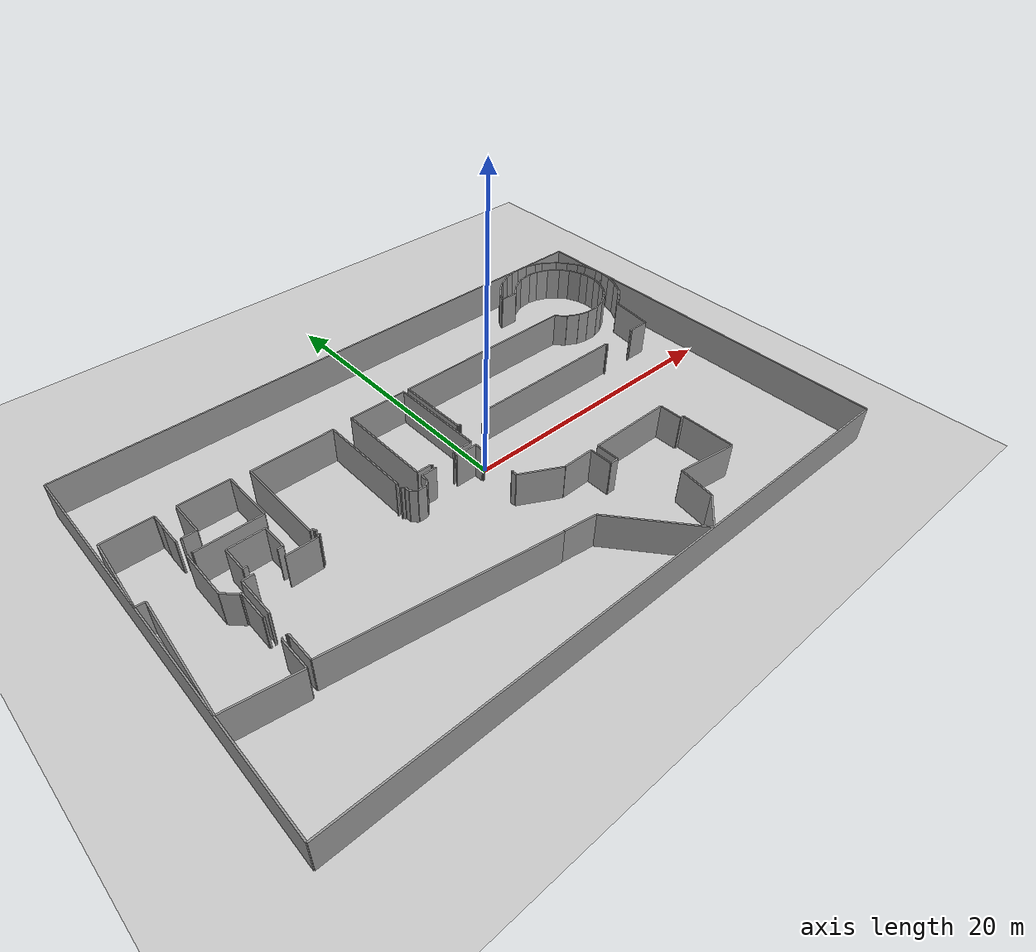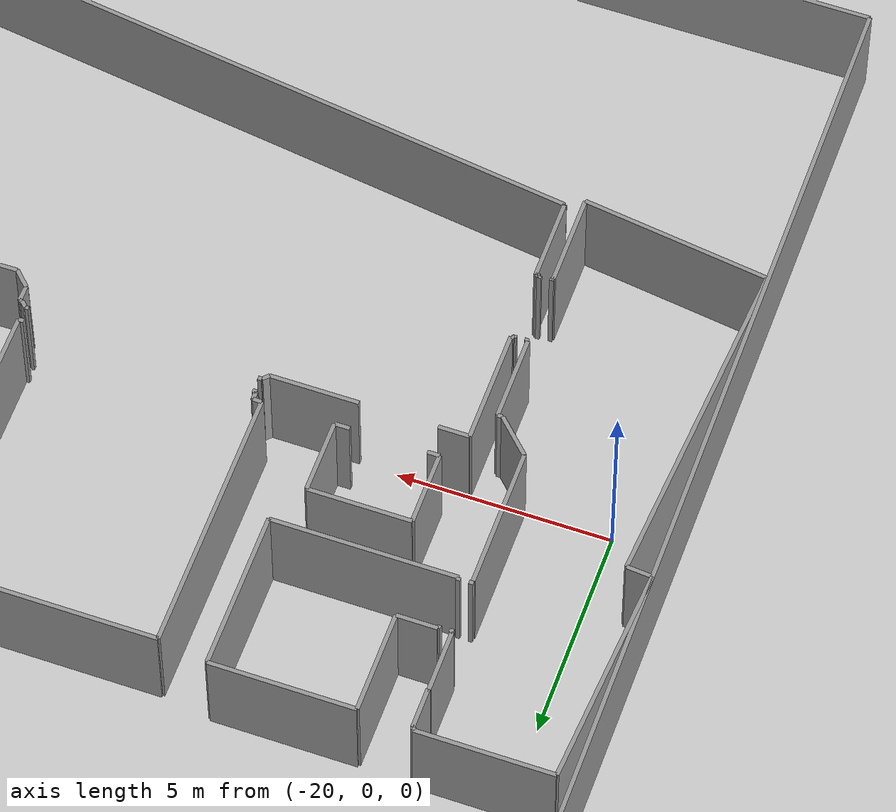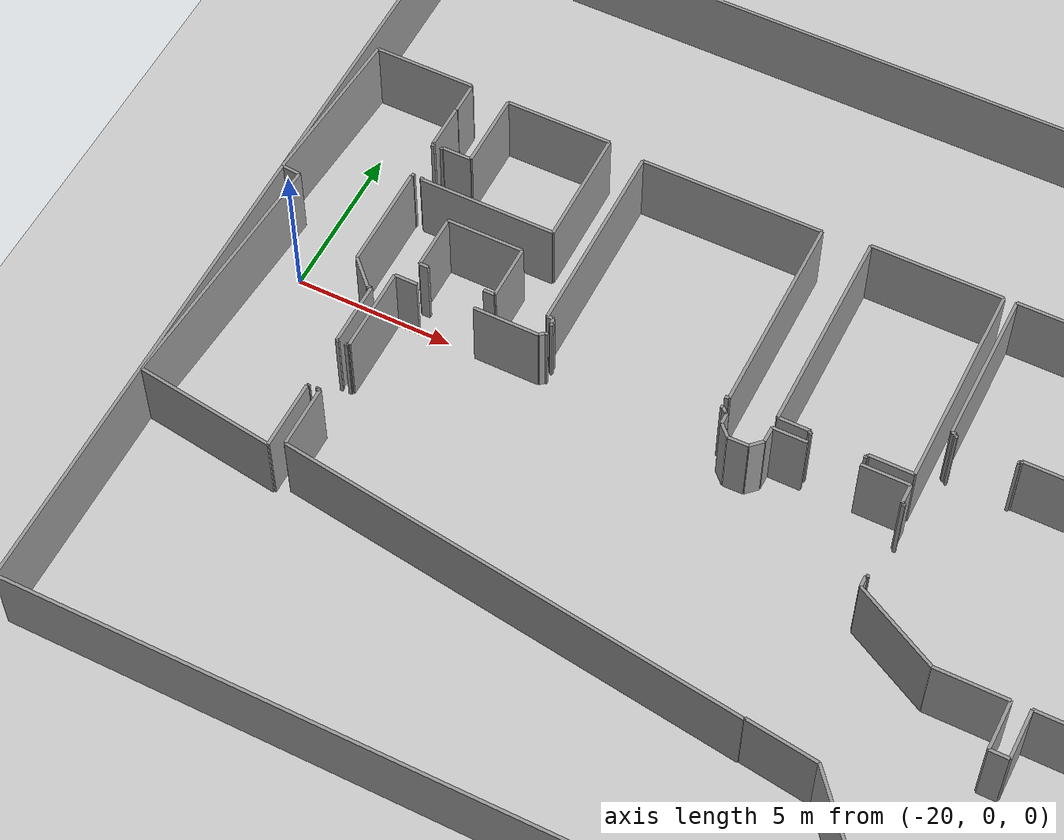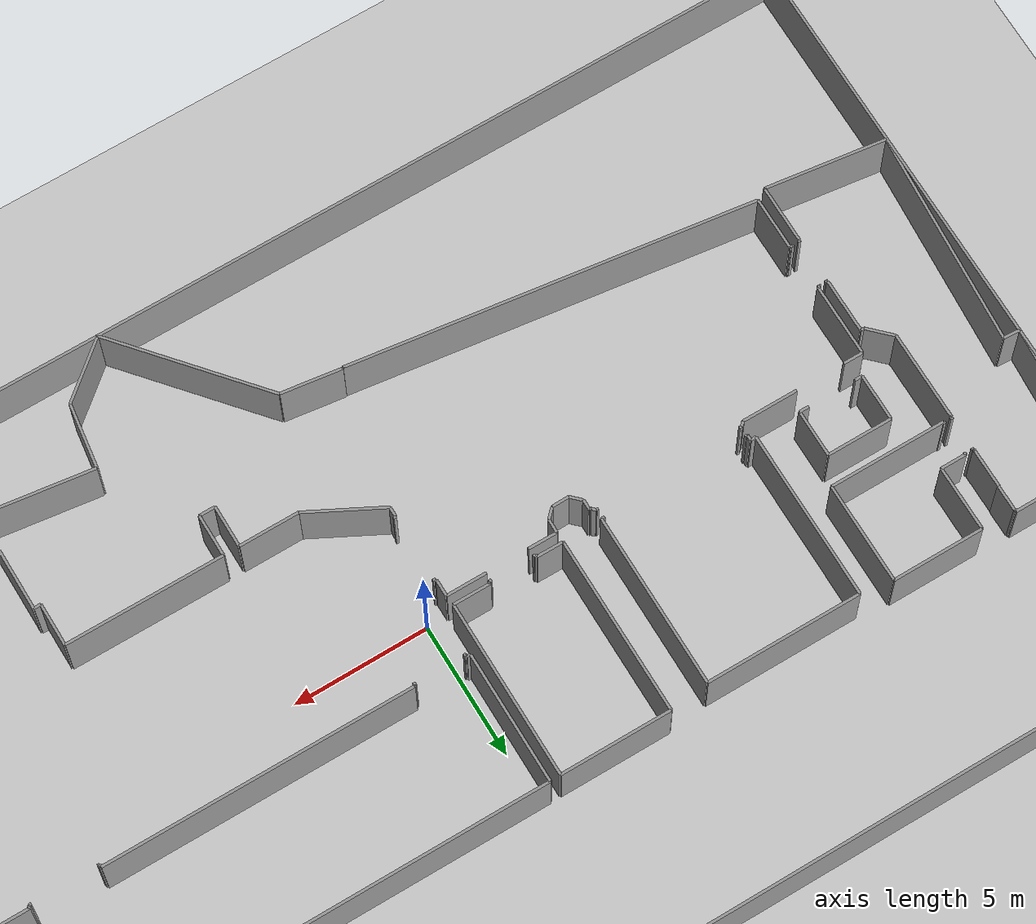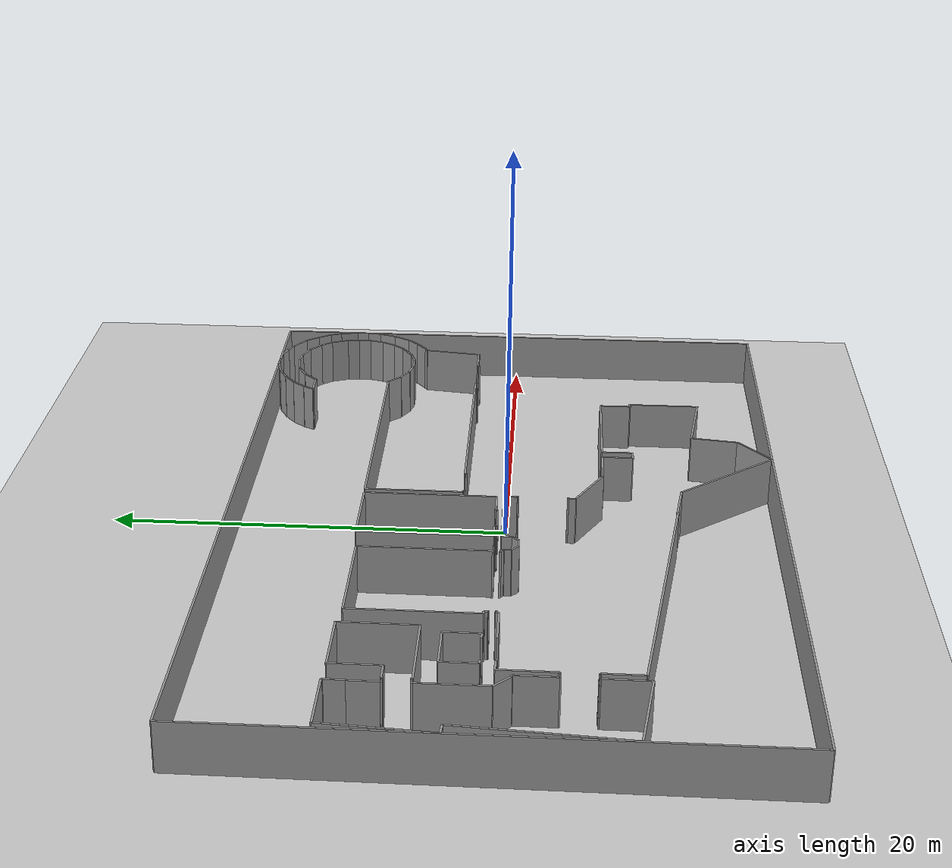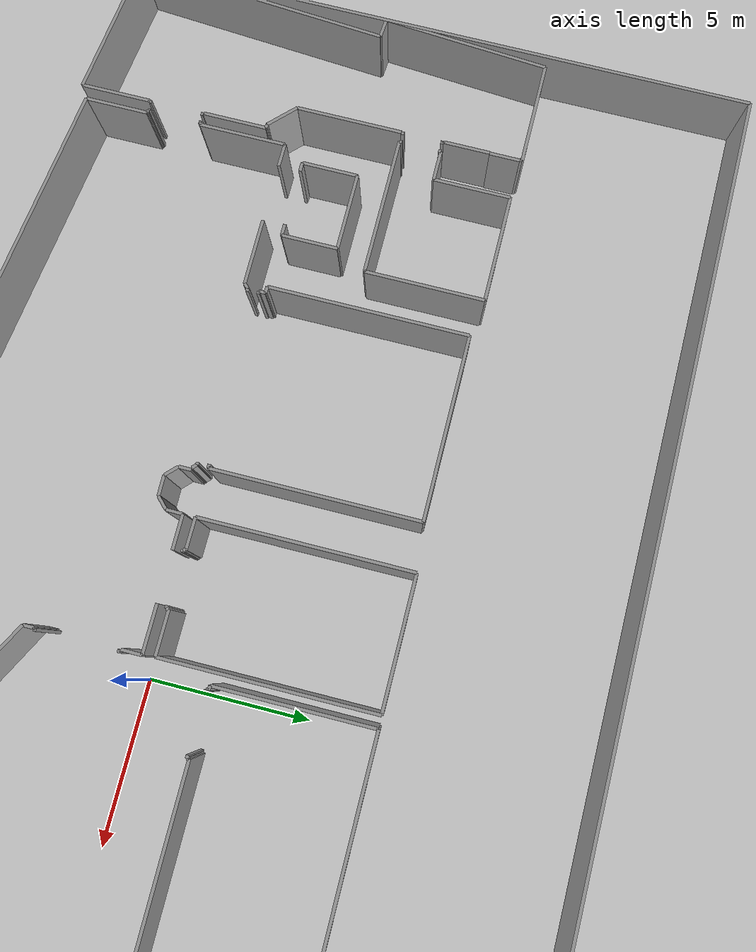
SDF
<sdf version="1.6">
  <world name="default">
    <light name="sun" type="directional">
      <cast_shadows>1</cast_shadows>
      <pose frame="">0 0 10 0 -0 0</pose>
      <diffuse>0.8 0.8 0.8 1</diffuse>
      <specular>0.1 0.1 0.1 1</specular>
      <attenuation>
        <range>1000</range>
        <constant>0.9</constant>
        <linear>0.01</linear>
        <quadratic>0.001</quadratic>
      </attenuation>
      <direction>-0.5 0.5 -1</direction>
    </light>
    <model name="ground_plane">
      <static>1</static>
      <link name="link">
        <collision name="collision">
          <geometry>
            <plane>
              <normal>0 0 1</normal>
              <size>100 100</size>
            </plane>
          </geometry>
          <surface>
            <friction>
              <ode>
                <mu>100</mu>
                <mu2>50</mu2>
              </ode>
              <torsional>
                <ode />
              </torsional>
            </friction>
            <contact>
              <ode />
            </contact>
            <bounce />
          </surface>
          <max_contacts>10</max_contacts>
        </collision>
        <visual name="visual">
          <cast_shadows>0</cast_shadows>
          <geometry>
            <plane>
              <normal>0 0 1</normal>
              <size>100 100</size>
            </plane>
          </geometry>
          <material>
            <script>
              <uri>file://media/materials/scripts/gazebo.material</uri>
              <name>Gazebo/Grey</name>
            </script>
          </material>
        </visual>
        <self_collide>0</self_collide>
        <kinematic>0</kinematic>
        <gravity>1</gravity>
      </link>
    </model>
    <gravity>0 0 -9.8</gravity>
    <magnetic_field>6e-06 2.3e-05 -4.2e-05</magnetic_field>
    <atmosphere type="adiabatic" />
    <physics default="0" name="default_physics" type="ode">
      <max_step_size>0.001</max_step_size>
      <real_time_factor>1</real_time_factor>
      <real_time_update_rate>1000</real_time_update_rate>
    </physics>
    <scene>
      <ambient>0.4 0.4 0.4 1</ambient>
      <background>0.7 0.7 0.7 1</background>
      <shadows>1</shadows>
    </scene>
    <spherical_coordinates>
      <surface_model>EARTH_WGS84</surface_model>
      <latitude_deg>0</latitude_deg>
      <longitude_deg>0</longitude_deg>
      <elevation>0</elevation>
      <heading_deg>0</heading_deg>
    </spherical_coordinates>
  <model name="0510030941_A_40_1_105">
		<static>1</static>
		<link name="Wall_0">
			<collision name="Wall_0_Collision">
				<geometry>
					<box>
						<size>8.01129009904 0.1 2.5</size>
					</box>
				</geometry>
				<pose frame="">4.00564504952 0 1.25 0 0 0</pose>
			</collision>
			<visual name="Wall_0_Visual">
				<pose frame="">4.00564504952 0 1.25 0 0 0</pose>
				<geometry>
					<box>
						<size>8.01129009904 0.1 2.5</size>
					</box>
				</geometry>
				<material>
					<script>
						<uri>file://media/materials/scripts/gazebo.material</uri>
						<name>Gazebo/Grey</name>
					</script>
					<ambient>1 1 1 1</ambient>
				</material>
			</visual>
			<pose frame="">0.0257898949348 -19.6818822812 0 0 0 1.49948547248</pose>
		</link>
		<link name="Wall_1">
			<collision name="Wall_1_Collision">
				<geometry>
					<box>
						<size>0.598456714326 0.1 2.5</size>
					</box>
				</geometry>
				<pose frame="">0.299228357163 0 1.25 0 0 0</pose>
			</collision>
			<visual name="Wall_1_Visual">
				<pose frame="">0.299228357163 0 1.25 0 0 0</pose>
				<geometry>
					<box>
						<size>0.598456714326 0.1 2.5</size>
					</box>
				</geometry>
				<material>
					<script>
						<uri>file://media/materials/scripts/gazebo.material</uri>
						<name>Gazebo/Grey</name>
					</script>
					<ambient>1 1 1 1</ambient>
				</material>
			</visual>
			<pose frame="">0.59659776657 -11.6909532098 0 0 0 3.06275300122</pose>
		</link>
		<link name="Wall_2">
			<collision name="Wall_2_Collision">
				<geometry>
					<box>
						<size>5.22019539742 0.1 2.5</size>
					</box>
				</geometry>
				<pose frame="">2.61009769871 0 1.25 0 0 0</pose>
			</collision>
			<visual name="Wall_2_Visual">
				<pose frame="">2.61009769871 0 1.25 0 0 0</pose>
				<geometry>
					<box>
						<size>5.22019539742 0.1 2.5</size>
					</box>
				</geometry>
				<material>
					<script>
						<uri>file://media/materials/scripts/gazebo.material</uri>
						<name>Gazebo/Grey</name>
					</script>
					<ambient>1 1 1 1</ambient>
				</material>
			</visual>
			<pose frame="">0.0 -11.6438199535 0 0 0 1.50111182906</pose>
		</link>
		<link name="Wall_3">
			<collision name="Wall_3_Collision">
				<geometry>
					<box>
						<size>3.20239350552 0.1 2.5</size>
					</box>
				</geometry>
				<pose frame="">1.60119675276 0 1.25 0 0 0</pose>
			</collision>
			<visual name="Wall_3_Visual">
				<pose frame="">1.60119675276 0 1.25 0 0 0</pose>
				<geometry>
					<box>
						<size>3.20239350552 0.1 2.5</size>
					</box>
				</geometry>
				<material>
					<script>
						<uri>file://media/materials/scripts/gazebo.material</uri>
						<name>Gazebo/Grey</name>
					</script>
					<ambient>1 1 1 1</ambient>
				</material>
			</visual>
			<pose frame="">0.363472361618 -6.43629387776 0 0 0 0.0</pose>
		</link>
		<link name="Wall_4">
			<collision name="Wall_4_Collision">
				<geometry>
					<box>
						<size>0.0754640275431 0.1 2.5</size>
					</box>
				</geometry>
				<pose frame="">0.0377320137715 0 1.25 0 0 0</pose>
			</collision>
			<visual name="Wall_4_Visual">
				<pose frame="">0.0377320137715 0 1.25 0 0 0</pose>
				<geometry>
					<box>
						<size>0.0754640275431 0.1 2.5</size>
					</box>
				</geometry>
				<material>
					<script>
						<uri>file://media/materials/scripts/gazebo.material</uri>
						<name>Gazebo/Grey</name>
					</script>
					<ambient>1 1 1 1</ambient>
				</material>
			</visual>
			<pose frame="">3.56586586714 -6.43629387776 0 0 0 -1.57079632679</pose>
		</link>
		<link name="Wall_5">
			<collision name="Wall_5_Collision">
				<geometry>
					<box>
						<size>0.0188024849771 0.1 2.5</size>
					</box>
				</geometry>
				<pose frame="">0.00940124248854 0 1.25 0 0 0</pose>
			</collision>
			<visual name="Wall_5_Visual">
				<pose frame="">0.00940124248854 0 1.25 0 0 0</pose>
				<geometry>
					<box>
						<size>0.0188024849771 0.1 2.5</size>
					</box>
				</geometry>
				<material>
					<script>
						<uri>file://media/materials/scripts/gazebo.material</uri>
						<name>Gazebo/Grey</name>
					</script>
					<ambient>1 1 1 1</ambient>
				</material>
			</visual>
			<pose frame="">3.56586586714 -6.5117579053 0 0 0 0.0</pose>
		</link>
		<link name="Wall_6">
			<collision name="Wall_6_Collision">
				<geometry>
					<box>
						<size>0.95308271823 0.1 2.5</size>
					</box>
				</geometry>
				<pose frame="">0.476541359115 0 1.25 0 0 0</pose>
			</collision>
			<visual name="Wall_6_Visual">
				<pose frame="">0.476541359115 0 1.25 0 0 0</pose>
				<geometry>
					<box>
						<size>0.95308271823 0.1 2.5</size>
					</box>
				</geometry>
				<material>
					<script>
						<uri>file://media/materials/scripts/gazebo.material</uri>
						<name>Gazebo/Grey</name>
					</script>
					<ambient>1 1 1 1</ambient>
				</material>
			</visual>
			<pose frame="">3.58466835211 -6.5117579053 0 0 0 -1.57079632679</pose>
		</link>
		<link name="Wall_7">
			<collision name="Wall_7_Collision">
				<geometry>
					<box>
						<size>0.0161345648114 0.1 2.5</size>
					</box>
				</geometry>
				<pose frame="">0.0080672824057 0 1.25 0 0 0</pose>
			</collision>
			<visual name="Wall_7_Visual">
				<pose frame="">0.0080672824057 0 1.25 0 0 0</pose>
				<geometry>
					<box>
						<size>0.0161345648114 0.1 2.5</size>
					</box>
				</geometry>
				<material>
					<script>
						<uri>file://media/materials/scripts/gazebo.material</uri>
						<name>Gazebo/Grey</name>
					</script>
					<ambient>1 1 1 1</ambient>
				</material>
			</visual>
			<pose frame="">3.58466835211 -7.46484062353 0 0 0 3.14159265359</pose>
		</link>
		<link name="Wall_8">
			<collision name="Wall_8_Collision">
				<geometry>
					<box>
						<size>1.45287309593 0.1 2.5</size>
					</box>
				</geometry>
				<pose frame="">0.726436547965 0 1.25 0 0 0</pose>
			</collision>
			<visual name="Wall_8_Visual">
				<pose frame="">0.726436547965 0 1.25 0 0 0</pose>
				<geometry>
					<box>
						<size>1.45287309593 0.1 2.5</size>
					</box>
				</geometry>
				<material>
					<script>
						<uri>file://media/materials/scripts/gazebo.material</uri>
						<name>Gazebo/Grey</name>
					</script>
					<ambient>1 1 1 1</ambient>
				</material>
			</visual>
			<pose frame="">3.5685337873 -7.46484062353 0 0 0 -1.57079632679</pose>
		</link>
		<link name="Wall_9">
			<collision name="Wall_9_Collision">
				<geometry>
					<box>
						<size>0.0223597118646 0.1 2.5</size>
					</box>
				</geometry>
				<pose frame="">0.0111798559323 0 1.25 0 0 0</pose>
			</collision>
			<visual name="Wall_9_Visual">
				<pose frame="">0.0111798559323 0 1.25 0 0 0</pose>
				<geometry>
					<box>
						<size>0.0223597118646 0.1 2.5</size>
					</box>
				</geometry>
				<material>
					<script>
						<uri>file://media/materials/scripts/gazebo.material</uri>
						<name>Gazebo/Grey</name>
					</script>
					<ambient>1 1 1 1</ambient>
				</material>
			</visual>
			<pose frame="">3.5685337873 -8.91771371946 0 0 0 0.0</pose>
		</link>
		<link name="Wall_10">
			<collision name="Wall_10_Collision">
				<geometry>
					<box>
						<size>0.0922338114416 0.1 2.5</size>
					</box>
				</geometry>
				<pose frame="">0.0461169057208 0 1.25 0 0 0</pose>
			</collision>
			<visual name="Wall_10_Visual">
				<pose frame="">0.0461169057208 0 1.25 0 0 0</pose>
				<geometry>
					<box>
						<size>0.0922338114416 0.1 2.5</size>
					</box>
				</geometry>
				<material>
					<script>
						<uri>file://media/materials/scripts/gazebo.material</uri>
						<name>Gazebo/Grey</name>
					</script>
					<ambient>1 1 1 1</ambient>
				</material>
			</visual>
			<pose frame="">3.59089349917 -8.91771371946 0 0 0 -1.57079632679</pose>
		</link>
		<link name="Wall_11">
			<collision name="Wall_11_Collision">
				<geometry>
					<box>
						<size>0.0983319146774 0.1 2.5</size>
					</box>
				</geometry>
				<pose frame="">0.0491659573387 0 1.25 0 0 0</pose>
			</collision>
			<visual name="Wall_11_Visual">
				<pose frame="">0.0491659573387 0 1.25 0 0 0</pose>
				<geometry>
					<box>
						<size>0.0983319146774 0.1 2.5</size>
					</box>
				</geometry>
				<material>
					<script>
						<uri>file://media/materials/scripts/gazebo.material</uri>
						<name>Gazebo/Grey</name>
					</script>
					<ambient>1 1 1 1</ambient>
				</material>
			</visual>
			<pose frame="">3.59089349917 -10.1680789704 0 0 0 -1.57079632679</pose>
		</link>
		<link name="Wall_12">
			<collision name="Wall_12_Collision">
				<geometry>
					<box>
						<size>0.0226137994995 0.1 2.5</size>
					</box>
				</geometry>
				<pose frame="">0.0113068997497 0 1.25 0 0 0</pose>
			</collision>
			<visual name="Wall_12_Visual">
				<pose frame="">0.0113068997497 0 1.25 0 0 0</pose>
				<geometry>
					<box>
						<size>0.0226137994995 0.1 2.5</size>
					</box>
				</geometry>
				<material>
					<script>
						<uri>file://media/materials/scripts/gazebo.material</uri>
						<name>Gazebo/Grey</name>
					</script>
					<ambient>1 1 1 1</ambient>
				</material>
			</visual>
			<pose frame="">3.59089349917 -10.2664108851 0 0 0 3.14159265359</pose>
		</link>
		<link name="Wall_13">
			<collision name="Wall_13_Collision">
				<geometry>
					<box>
						<size>3.32232286916 0.1 2.5</size>
					</box>
				</geometry>
				<pose frame="">1.66116143458 0 1.25 0 0 0</pose>
			</collision>
			<visual name="Wall_13_Visual">
				<pose frame="">1.66116143458 0 1.25 0 0 0</pose>
				<geometry>
					<box>
						<size>3.32232286916 0.1 2.5</size>
					</box>
				</geometry>
				<material>
					<script>
						<uri>file://media/materials/scripts/gazebo.material</uri>
						<name>Gazebo/Grey</name>
					</script>
					<ambient>1 1 1 1</ambient>
				</material>
			</visual>
			<pose frame="">3.56827969967 -10.2664108851 0 0 0 -1.57079632679</pose>
		</link>
		<link name="Wall_14">
			<collision name="Wall_14_Collision">
				<geometry>
					<box>
						<size>1.08204522984 0.1 2.5</size>
					</box>
				</geometry>
				<pose frame="">0.541022614922 0 1.25 0 0 0</pose>
			</collision>
			<visual name="Wall_14_Visual">
				<pose frame="">0.541022614922 0 1.25 0 0 0</pose>
				<geometry>
					<box>
						<size>1.08204522984 0.1 2.5</size>
					</box>
				</geometry>
				<material>
					<script>
						<uri>file://media/materials/scripts/gazebo.material</uri>
						<name>Gazebo/Grey</name>
					</script>
					<ambient>1 1 1 1</ambient>
				</material>
			</visual>
			<pose frame="">3.56827969967 -13.5887337543 0 0 0 -0.785979317338</pose>
		</link>
		<link name="Wall_15">
			<collision name="Wall_15_Collision">
				<geometry>
					<box>
						<size>0.117388487289 0.1 2.5</size>
					</box>
				</geometry>
				<pose frame="">0.0586942436446 0 1.25 0 0 0</pose>
			</collision>
			<visual name="Wall_15_Visual">
				<pose frame="">0.0586942436446 0 1.25 0 0 0</pose>
				<geometry>
					<box>
						<size>0.117388487289 0.1 2.5</size>
					</box>
				</geometry>
				<material>
					<script>
						<uri>file://media/materials/scripts/gazebo.material</uri>
						<name>Gazebo/Grey</name>
					</script>
					<ambient>1 1 1 1</ambient>
				</material>
			</visual>
			<pose frame="">4.33295643668 -14.354299798 0 0 0 0.0</pose>
		</link>
		<link name="Wall_16">
			<collision name="Wall_16_Collision">
				<geometry>
					<box>
						<size>2.00907092856 0.1 2.5</size>
					</box>
				</geometry>
				<pose frame="">1.00453546428 0 1.25 0 0 0</pose>
			</collision>
			<visual name="Wall_16_Visual">
				<pose frame="">1.00453546428 0 1.25 0 0 0</pose>
				<geometry>
					<box>
						<size>2.00907092856 0.1 2.5</size>
					</box>
				</geometry>
				<material>
					<script>
						<uri>file://media/materials/scripts/gazebo.material</uri>
						<name>Gazebo/Grey</name>
					</script>
					<ambient>1 1 1 1</ambient>
				</material>
			</visual>
			<pose frame="">4.45034492396 -14.354299798 0 0 0 -1.57079632679</pose>
		</link>
		<link name="Wall_17">
			<collision name="Wall_17_Collision">
				<geometry>
					<box>
						<size>0.0332854801621 0.1 2.5</size>
					</box>
				</geometry>
				<pose frame="">0.016642740081 0 1.25 0 0 0</pose>
			</collision>
			<visual name="Wall_17_Visual">
				<pose frame="">0.016642740081 0 1.25 0 0 0</pose>
				<geometry>
					<box>
						<size>0.0332854801621 0.1 2.5</size>
					</box>
				</geometry>
				<material>
					<script>
						<uri>file://media/materials/scripts/gazebo.material</uri>
						<name>Gazebo/Grey</name>
					</script>
					<ambient>1 1 1 1</ambient>
				</material>
			</visual>
			<pose frame="">4.45034492396 -16.3633707266 0 0 0 0.0</pose>
		</link>
		<link name="Wall_18">
			<collision name="Wall_18_Collision">
				<geometry>
					<box>
						<size>0.0719068006555 0.1 2.5</size>
					</box>
				</geometry>
				<pose frame="">0.0359534003278 0 1.25 0 0 0</pose>
			</collision>
			<visual name="Wall_18_Visual">
				<pose frame="">0.0359534003278 0 1.25 0 0 0</pose>
				<geometry>
					<box>
						<size>0.0719068006555 0.1 2.5</size>
					</box>
				</geometry>
				<material>
					<script>
						<uri>file://media/materials/scripts/gazebo.material</uri>
						<name>Gazebo/Grey</name>
					</script>
					<ambient>1 1 1 1</ambient>
				</material>
			</visual>
			<pose frame="">4.48363040413 -16.3633707266 0 0 0 -1.57079632679</pose>
		</link>
		<link name="Wall_19">
			<collision name="Wall_19_Collision">
				<geometry>
					<box>
						<size>0.0617432952625 0.1 2.5</size>
					</box>
				</geometry>
				<pose frame="">0.0308716476313 0 1.25 0 0 0</pose>
			</collision>
			<visual name="Wall_19_Visual">
				<pose frame="">0.0308716476313 0 1.25 0 0 0</pose>
				<geometry>
					<box>
						<size>0.0617432952625 0.1 2.5</size>
					</box>
				</geometry>
				<material>
					<script>
						<uri>file://media/materials/scripts/gazebo.material</uri>
						<name>Gazebo/Grey</name>
					</script>
					<ambient>1 1 1 1</ambient>
				</material>
			</visual>
			<pose frame="">4.48363040413 -18.0291692605 0 0 0 -1.57079632679</pose>
		</link>
		<link name="Wall_20">
			<collision name="Wall_20_Collision">
				<geometry>
					<box>
						<size>0.0293471218223 0.1 2.5</size>
					</box>
				</geometry>
				<pose frame="">0.0146735609112 0 1.25 0 0 0</pose>
			</collision>
			<visual name="Wall_20_Visual">
				<pose frame="">0.0146735609112 0 1.25 0 0 0</pose>
				<geometry>
					<box>
						<size>0.0293471218223 0.1 2.5</size>
					</box>
				</geometry>
				<material>
					<script>
						<uri>file://media/materials/scripts/gazebo.material</uri>
						<name>Gazebo/Grey</name>
					</script>
					<ambient>1 1 1 1</ambient>
				</material>
			</visual>
			<pose frame="">4.48363040413 -18.0909125557 0 0 0 3.14159265359</pose>
		</link>
		<link name="Wall_21">
			<collision name="Wall_21_Collision">
				<geometry>
					<box>
						<size>2.18134234497 0.1 2.5</size>
					</box>
				</geometry>
				<pose frame="">1.09067117249 0 1.25 0 0 0</pose>
			</collision>
			<visual name="Wall_21_Visual">
				<pose frame="">1.09067117249 0 1.25 0 0 0</pose>
				<geometry>
					<box>
						<size>2.18134234497 0.1 2.5</size>
					</box>
				</geometry>
				<material>
					<script>
						<uri>file://media/materials/scripts/gazebo.material</uri>
						<name>Gazebo/Grey</name>
					</script>
					<ambient>1 1 1 1</ambient>
				</material>
			</visual>
			<pose frame="">4.4542832823 -18.0909125557 0 0 0 -1.57079632679</pose>
		</link>
		<link name="Wall_22">
			<collision name="Wall_22_Collision">
				<geometry>
					<box>
						<size>4.46767204614 0.1 2.5</size>
					</box>
				</geometry>
				<pose frame="">2.23383602307 0 1.25 0 0 0</pose>
			</collision>
			<visual name="Wall_22_Visual">
				<pose frame="">2.23383602307 0 1.25 0 0 0</pose>
				<geometry>
					<box>
						<size>4.46767204614 0.1 2.5</size>
					</box>
				</geometry>
				<material>
					<script>
						<uri>file://media/materials/scripts/gazebo.material</uri>
						<name>Gazebo/Grey</name>
					</script>
					<ambient>1 1 1 1</ambient>
				</material>
			</visual>
			<pose frame="">4.4542832823 -20.2722549007 0 0 0 3.00906179161</pose>
		</link>
		<link name="Wall_23">
			<collision name="Wall_23_Collision">
				<geometry>
					<box>
						<size>0.944316694828 0.1 2.5</size>
					</box>
				</geometry>
				<pose frame="">0.472158347414 0 1.25 0 0 0</pose>
			</collision>
			<visual name="Wall_23_Visual">
				<pose frame="">0.472158347414 0 1.25 0 0 0</pose>
				<geometry>
					<box>
						<size>0.944316694828 0.1 2.5</size>
					</box>
				</geometry>
				<material>
					<script>
						<uri>file://media/materials/scripts/gazebo.material</uri>
						<name>Gazebo/Grey</name>
					</script>
					<ambient>1 1 1 1</ambient>
				</material>
			</visual>
			<pose frame="">3.8880489881 -8.92660678668 0 0 0 0.0</pose>
		</link>
		<link name="Wall_24">
			<collision name="Wall_24_Collision">
				<geometry>
					<box>
						<size>2.41230800503 0.1 2.5</size>
					</box>
				</geometry>
				<pose frame="">1.20615400252 0 1.25 0 0 0</pose>
			</collision>
			<visual name="Wall_24_Visual">
				<pose frame="">1.20615400252 0 1.25 0 0 0</pose>
				<geometry>
					<box>
						<size>2.41230800503 0.1 2.5</size>
					</box>
				</geometry>
				<material>
					<script>
						<uri>file://media/materials/scripts/gazebo.material</uri>
						<name>Gazebo/Grey</name>
					</script>
					<ambient>1 1 1 1</ambient>
				</material>
			</visual>
			<pose frame="">4.83236568292 -8.92660678668 0 0 0 1.57079632679</pose>
		</link>
		<link name="Wall_25">
			<collision name="Wall_25_Collision">
				<geometry>
					<box>
						<size>3.37530014102 0.1 2.5</size>
					</box>
				</geometry>
				<pose frame="">1.68765007051 0 1.25 0 0 0</pose>
			</collision>
			<visual name="Wall_25_Visual">
				<pose frame="">1.68765007051 0 1.25 0 0 0</pose>
				<geometry>
					<box>
						<size>3.37530014102 0.1 2.5</size>
					</box>
				</geometry>
				<material>
					<script>
						<uri>file://media/materials/scripts/gazebo.material</uri>
						<name>Gazebo/Grey</name>
					</script>
					<ambient>1 1 1 1</ambient>
				</material>
			</visual>
			<pose frame="">4.83236568292 -6.51429878165 0 0 0 0.0</pose>
		</link>
		<link name="Wall_26">
			<collision name="Wall_26_Collision">
				<geometry>
					<box>
						<size>3.73242031177 0.1 2.5</size>
					</box>
				</geometry>
				<pose frame="">1.86621015588 0 1.25 0 0 0</pose>
			</collision>
			<visual name="Wall_26_Visual">
				<pose frame="">1.86621015588 0 1.25 0 0 0</pose>
				<geometry>
					<box>
						<size>3.73242031177 0.1 2.5</size>
					</box>
				</geometry>
				<material>
					<script>
						<uri>file://media/materials/scripts/gazebo.material</uri>
						<name>Gazebo/Grey</name>
					</script>
					<ambient>1 1 1 1</ambient>
				</material>
			</visual>
			<pose frame="">8.20766582394 -6.51429878165 0 0 0 -1.57079632679</pose>
		</link>
		<link name="Wall_27">
			<collision name="Wall_27_Collision">
				<geometry>
					<box>
						<size>4.32825581543 0.1 2.5</size>
					</box>
				</geometry>
				<pose frame="">2.16412790772 0 1.25 0 0 0</pose>
			</collision>
			<visual name="Wall_27_Visual">
				<pose frame="">2.16412790772 0 1.25 0 0 0</pose>
				<geometry>
					<box>
						<size>4.32825581543 0.1 2.5</size>
					</box>
				</geometry>
				<material>
					<script>
						<uri>file://media/materials/scripts/gazebo.material</uri>
						<name>Gazebo/Grey</name>
					</script>
					<ambient>1 1 1 1</ambient>
				</material>
			</visual>
			<pose frame="">8.20766582394 -10.2467190934 0 0 0 3.14159265359</pose>
		</link>
		<link name="Wall_28">
			<collision name="Wall_28_Collision">
				<geometry>
					<box>
						<size>0.0818162184137 0.1 2.5</size>
					</box>
				</geometry>
				<pose frame="">0.0409081092069 0 1.25 0 0 0</pose>
			</collision>
			<visual name="Wall_28_Visual">
				<pose frame="">0.0409081092069 0 1.25 0 0 0</pose>
				<geometry>
					<box>
						<size>0.0818162184137 0.1 2.5</size>
					</box>
				</geometry>
				<material>
					<script>
						<uri>file://media/materials/scripts/gazebo.material</uri>
						<name>Gazebo/Grey</name>
					</script>
					<ambient>1 1 1 1</ambient>
				</material>
			</visual>
			<pose frame="">3.87941000851 -10.2467190934 0 0 0 1.57079632679</pose>
		</link>
		<link name="Wall_29">
			<collision name="Wall_29_Collision">
				<geometry>
					<box>
						<size>0.0787343744685 0.1 2.5</size>
					</box>
				</geometry>
				<pose frame="">0.0393671872343 0 1.25 0 0 0</pose>
			</collision>
			<visual name="Wall_29_Visual">
				<pose frame="">0.0393671872343 0 1.25 0 0 0</pose>
				<geometry>
					<box>
						<size>0.0787343744685 0.1 2.5</size>
					</box>
				</geometry>
				<material>
					<script>
						<uri>file://media/materials/scripts/gazebo.material</uri>
						<name>Gazebo/Grey</name>
					</script>
					<ambient>1 1 1 1</ambient>
				</material>
			</visual>
			<pose frame="">3.87941000851 -9.00486577821 0 0 0 1.46085186388</pose>
		</link>
		<link name="Wall_30">
			<collision name="Wall_30_Collision">
				<geometry>
					<box>
						<size>1.9465653704 0.1 2.5</size>
					</box>
				</geometry>
				<pose frame="">0.973282685198 0 1.25 0 0 0</pose>
			</collision>
			<visual name="Wall_30_Visual">
				<pose frame="">0.973282685198 0 1.25 0 0 0</pose>
				<geometry>
					<box>
						<size>1.9465653704 0.1 2.5</size>
					</box>
				</geometry>
				<material>
					<script>
						<uri>file://media/materials/scripts/gazebo.material</uri>
						<name>Gazebo/Grey</name>
					</script>
					<ambient>1 1 1 1</ambient>
				</material>
			</visual>
			<pose frame="">4.85802853404 -20.0095282863 0 0 0 1.57079632679</pose>
		</link>
		<link name="Wall_31">
			<collision name="Wall_31_Collision">
				<geometry>
					<box>
						<size>0.0938853810679 0.1 2.5</size>
					</box>
				</geometry>
				<pose frame="">0.046942690534 0 1.25 0 0 0</pose>
			</collision>
			<visual name="Wall_31_Visual">
				<pose frame="">0.046942690534 0 1.25 0 0 0</pose>
				<geometry>
					<box>
						<size>0.0938853810679 0.1 2.5</size>
					</box>
				</geometry>
				<material>
					<script>
						<uri>file://media/materials/scripts/gazebo.material</uri>
						<name>Gazebo/Grey</name>
					</script>
					<ambient>1 1 1 1</ambient>
				</material>
			</visual>
			<pose frame="">4.85802853404 -18.0629629159 0 0 0 3.14159265359</pose>
		</link>
		<link name="Wall_32">
			<collision name="Wall_32_Collision">
				<geometry>
					<box>
						<size>0.0650464345153 0.1 2.5</size>
					</box>
				</geometry>
				<pose frame="">0.0325232172576 0 1.25 0 0 0</pose>
			</collision>
			<visual name="Wall_32_Visual">
				<pose frame="">0.0325232172576 0 1.25 0 0 0</pose>
				<geometry>
					<box>
						<size>0.0650464345153 0.1 2.5</size>
					</box>
				</geometry>
				<material>
					<script>
						<uri>file://media/materials/scripts/gazebo.material</uri>
						<name>Gazebo/Grey</name>
					</script>
					<ambient>1 1 1 1</ambient>
				</material>
			</visual>
			<pose frame="">4.76414315297 -18.0629629159 0 0 0 1.57079632679</pose>
		</link>
		<link name="Wall_33">
			<collision name="Wall_33_Collision">
				<geometry>
					<box>
						<size>0.0702552310292 0.1 2.5</size>
					</box>
				</geometry>
				<pose frame="">0.0351276155146 0 1.25 0 0 0</pose>
			</collision>
			<visual name="Wall_33_Visual">
				<pose frame="">0.0351276155146 0 1.25 0 0 0</pose>
				<geometry>
					<box>
						<size>0.0702552310292 0.1 2.5</size>
					</box>
				</geometry>
				<material>
					<script>
						<uri>file://media/materials/scripts/gazebo.material</uri>
						<name>Gazebo/Grey</name>
					</script>
					<ambient>1 1 1 1</ambient>
				</material>
			</visual>
			<pose frame="">4.76414315297 -16.4234624522 0 0 0 1.57079632679</pose>
		</link>
		<link name="Wall_34">
			<collision name="Wall_34_Collision">
				<geometry>
					<box>
						<size>0.0730501950123 0.1 2.5</size>
					</box>
				</geometry>
				<pose frame="">0.0365250975061 0 1.25 0 0 0</pose>
			</collision>
			<visual name="Wall_34_Visual">
				<pose frame="">0.0365250975061 0 1.25 0 0 0</pose>
				<geometry>
					<box>
						<size>0.0730501950123 0.1 2.5</size>
					</box>
				</geometry>
				<material>
					<script>
						<uri>file://media/materials/scripts/gazebo.material</uri>
						<name>Gazebo/Grey</name>
					</script>
					<ambient>1 1 1 1</ambient>
				</material>
			</visual>
			<pose frame="">4.76414315297 -16.3532072212 0 0 0 0.0</pose>
		</link>
		<link name="Wall_35">
			<collision name="Wall_35_Collision">
				<geometry>
					<box>
						<size>2.70692261761 0.1 2.5</size>
					</box>
				</geometry>
				<pose frame="">1.35346130881 0 1.25 0 0 0</pose>
			</collision>
			<visual name="Wall_35_Visual">
				<pose frame="">1.35346130881 0 1.25 0 0 0</pose>
				<geometry>
					<box>
						<size>2.70692261761 0.1 2.5</size>
					</box>
				</geometry>
				<material>
					<script>
						<uri>file://media/materials/scripts/gazebo.material</uri>
						<name>Gazebo/Grey</name>
					</script>
					<ambient>1 1 1 1</ambient>
				</material>
			</visual>
			<pose frame="">4.83719334799 -16.3532072212 0 0 0 1.57079632679</pose>
		</link>
		<link name="Wall_36">
			<collision name="Wall_36_Collision">
				<geometry>
					<box>
						<size>0.726182460331 0.1 2.5</size>
					</box>
				</geometry>
				<pose frame="">0.363091230165 0 1.25 0 0 0</pose>
			</collision>
			<visual name="Wall_36_Visual">
				<pose frame="">0.363091230165 0 1.25 0 0 0</pose>
				<geometry>
					<box>
						<size>0.726182460331 0.1 2.5</size>
					</box>
				</geometry>
				<material>
					<script>
						<uri>file://media/materials/scripts/gazebo.material</uri>
						<name>Gazebo/Grey</name>
					</script>
					<ambient>1 1 1 1</ambient>
				</material>
			</visual>
			<pose frame="">4.83719334799 -13.6462846036 0 0 0 0.0</pose>
		</link>
		<link name="Wall_37">
			<collision name="Wall_37_Collision">
				<geometry>
					<box>
						<size>2.07017900474 0.1 2.5</size>
					</box>
				</geometry>
				<pose frame="">1.03508950237 0 1.25 0 0 0</pose>
			</collision>
			<visual name="Wall_37_Visual">
				<pose frame="">1.03508950237 0 1.25 0 0 0</pose>
				<geometry>
					<box>
						<size>2.07017900474 0.1 2.5</size>
					</box>
				</geometry>
				<material>
					<script>
						<uri>file://media/materials/scripts/gazebo.material</uri>
						<name>Gazebo/Grey</name>
					</script>
					<ambient>1 1 1 1</ambient>
				</material>
			</visual>
			<pose frame="">7.386581632 -13.6462846036 0 0 0 0.0</pose>
		</link>
		<link name="Wall_38">
			<collision name="Wall_38_Collision">
				<geometry>
					<box>
						<size>0.187940363819 0.1 2.5</size>
					</box>
				</geometry>
				<pose frame="">0.0939701819095 0 1.25 0 0 0</pose>
			</collision>
			<visual name="Wall_38_Visual">
				<pose frame="">0.0939701819095 0 1.25 0 0 0</pose>
				<geometry>
					<box>
						<size>0.187940363819 0.1 2.5</size>
					</box>
				</geometry>
				<material>
					<script>
						<uri>file://media/materials/scripts/gazebo.material</uri>
						<name>Gazebo/Grey</name>
					</script>
					<ambient>1 1 1 1</ambient>
				</material>
			</visual>
			<pose frame="">9.45676063674 -13.6462846036 0 0 0 0.794958101597</pose>
		</link>
		<link name="Wall_39">
			<collision name="Wall_39_Collision">
				<geometry>
					<box>
						<size>0.088676584554 0.1 2.5</size>
					</box>
				</geometry>
				<pose frame="">0.044338292277 0 1.25 0 0 0</pose>
			</collision>
			<visual name="Wall_39_Visual">
				<pose frame="">0.044338292277 0 1.25 0 0 0</pose>
				<geometry>
					<box>
						<size>0.088676584554 0.1 2.5</size>
					</box>
				</geometry>
				<material>
					<script>
						<uri>file://media/materials/scripts/gazebo.material</uri>
						<name>Gazebo/Grey</name>
					</script>
					<ambient>1 1 1 1</ambient>
				</material>
			</visual>
			<pose frame="">9.58837803158 -13.5121263324 0 0 0 0.0</pose>
		</link>
		<link name="Wall_40">
			<collision name="Wall_40_Collision">
				<geometry>
					<box>
						<size>0.0764803780824 0.1 2.5</size>
					</box>
				</geometry>
				<pose frame="">0.0382401890412 0 1.25 0 0 0</pose>
			</collision>
			<visual name="Wall_40_Visual">
				<pose frame="">0.0382401890412 0 1.25 0 0 0</pose>
				<geometry>
					<box>
						<size>0.0764803780824 0.1 2.5</size>
					</box>
				</geometry>
				<material>
					<script>
						<uri>file://media/materials/scripts/gazebo.material</uri>
						<name>Gazebo/Grey</name>
					</script>
					<ambient>1 1 1 1</ambient>
				</material>
			</visual>
			<pose frame="">15.0497376545 -13.5121263324 0 0 0 0.0</pose>
		</link>
		<link name="Wall_41">
			<collision name="Wall_41_Collision">
				<geometry>
					<box>
						<size>0.181038866264 0.1 2.5</size>
					</box>
				</geometry>
				<pose frame="">0.0905194331321 0 1.25 0 0 0</pose>
			</collision>
			<visual name="Wall_41_Visual">
				<pose frame="">0.0905194331321 0 1.25 0 0 0</pose>
				<geometry>
					<box>
						<size>0.181038866264 0.1 2.5</size>
					</box>
				</geometry>
				<material>
					<script>
						<uri>file://media/materials/scripts/gazebo.material</uri>
						<name>Gazebo/Grey</name>
					</script>
					<ambient>1 1 1 1</ambient>
				</material>
			</visual>
			<pose frame="">15.1262180326 -13.5121263324 0 0 0 -0.769022456129</pose>
		</link>
		<link name="Wall_42">
			<collision name="Wall_42_Collision">
				<geometry>
					<box>
						<size>0.0536124909481 0.1 2.5</size>
					</box>
				</geometry>
				<pose frame="">0.0268062454741 0 1.25 0 0 0</pose>
			</collision>
			<visual name="Wall_42_Visual">
				<pose frame="">0.0268062454741 0 1.25 0 0 0</pose>
				<geometry>
					<box>
						<size>0.0536124909481 0.1 2.5</size>
					</box>
				</geometry>
				<material>
					<script>
						<uri>file://media/materials/scripts/gazebo.material</uri>
						<name>Gazebo/Grey</name>
					</script>
					<ambient>1 1 1 1</ambient>
				</material>
			</visual>
			<pose frame="">15.2563109016 -13.6380267554 0 0 0 0.0</pose>
		</link>
		<link name="Wall_43">
			<collision name="Wall_43_Collision">
				<geometry>
					<box>
						<size>0.377828312985 0.1 2.5</size>
					</box>
				</geometry>
				<pose frame="">0.188914156493 0 1.25 0 0 0</pose>
			</collision>
			<visual name="Wall_43_Visual">
				<pose frame="">0.188914156493 0 1.25 0 0 0</pose>
				<geometry>
					<box>
						<size>0.377828312985 0.1 2.5</size>
					</box>
				</geometry>
				<material>
					<script>
						<uri>file://media/materials/scripts/gazebo.material</uri>
						<name>Gazebo/Grey</name>
					</script>
					<ambient>1 1 1 1</ambient>
				</material>
			</visual>
			<pose frame="">15.3099233926 -13.6380267554 0 0 0 -1.57079632679</pose>
		</link>
		<link name="Wall_44">
			<collision name="Wall_44_Collision">
				<geometry>
					<box>
						<size>0.483323706376 0.1 2.5</size>
					</box>
				</geometry>
				<pose frame="">0.241661853188 0 1.25 0 0 0</pose>
			</collision>
			<visual name="Wall_44_Visual">
				<pose frame="">0.241661853188 0 1.25 0 0 0</pose>
				<geometry>
					<box>
						<size>0.483323706376 0.1 2.5</size>
					</box>
				</geometry>
				<material>
					<script>
						<uri>file://media/materials/scripts/gazebo.material</uri>
						<name>Gazebo/Grey</name>
					</script>
					<ambient>1 1 1 1</ambient>
				</material>
			</visual>
			<pose frame="">15.3099233926 -14.0158550684 0 0 0 -0.776476467032</pose>
		</link>
		<link name="Wall_45">
			<collision name="Wall_45_Collision">
				<geometry>
					<box>
						<size>0.629842362305 0.1 2.5</size>
					</box>
				</geometry>
				<pose frame="">0.314921181152 0 1.25 0 0 0</pose>
			</collision>
			<visual name="Wall_45_Visual">
				<pose frame="">0.314921181152 0 1.25 0 0 0</pose>
				<geometry>
					<box>
						<size>0.629842362305 0.1 2.5</size>
					</box>
				</geometry>
				<material>
					<script>
						<uri>file://media/materials/scripts/gazebo.material</uri>
						<name>Gazebo/Grey</name>
					</script>
					<ambient>1 1 1 1</ambient>
				</material>
			</visual>
			<pose frame="">15.654720313 -14.3545538856 0 0 0 0.0165407548028</pose>
		</link>
		<link name="Wall_46">
			<collision name="Wall_46_Collision">
				<geometry>
					<box>
						<size>0.458430164429 0.1 2.5</size>
					</box>
				</geometry>
				<pose frame="">0.229215082215 0 1.25 0 0 0</pose>
			</collision>
			<visual name="Wall_46_Visual">
				<pose frame="">0.229215082215 0 1.25 0 0 0</pose>
				<geometry>
					<box>
						<size>0.458430164429 0.1 2.5</size>
					</box>
				</geometry>
				<material>
					<script>
						<uri>file://media/materials/scripts/gazebo.material</uri>
						<name>Gazebo/Grey</name>
					</script>
					<ambient>1 1 1 1</ambient>
				</material>
			</visual>
			<pose frame="">16.284476516 -14.3441362926 0 0 0 0.778931469296</pose>
		</link>
		<link name="Wall_47">
			<collision name="Wall_47_Collision">
				<geometry>
					<box>
						<size>0.51117464106 0.1 2.5</size>
					</box>
				</geometry>
				<pose frame="">0.25558732053 0 1.25 0 0 0</pose>
			</collision>
			<visual name="Wall_47_Visual">
				<pose frame="">0.25558732053 0 1.25 0 0 0</pose>
				<geometry>
					<box>
						<size>0.51117464106 0.1 2.5</size>
					</box>
				</geometry>
				<material>
					<script>
						<uri>file://media/materials/scripts/gazebo.material</uri>
						<name>Gazebo/Grey</name>
					</script>
					<ambient>1 1 1 1</ambient>
				</material>
			</visual>
			<pose frame="">16.6107250391 -14.0220802155 0 0 0 1.55339813218</pose>
		</link>
		<link name="Wall_48">
			<collision name="Wall_48_Collision">
				<geometry>
					<box>
						<size>1.07415674591 0.1 2.5</size>
					</box>
				</geometry>
				<pose frame="">0.537078372955 0 1.25 0 0 0</pose>
			</collision>
			<visual name="Wall_48_Visual">
				<pose frame="">0.537078372955 0 1.25 0 0 0</pose>
				<geometry>
					<box>
						<size>1.07415674591 0.1 2.5</size>
					</box>
				</geometry>
				<material>
					<script>
						<uri>file://media/materials/scripts/gazebo.material</uri>
						<name>Gazebo/Grey</name>
					</script>
					<ambient>1 1 1 1</ambient>
				</material>
			</visual>
			<pose frame="">16.6196181063 -13.510982938 0 0 0 0.00153755053291</pose>
		</link>
		<link name="Wall_49">
			<collision name="Wall_49_Collision">
				<geometry>
					<box>
						<size>1.49594095003 0.1 2.5</size>
					</box>
				</geometry>
				<pose frame="">0.747970475017 0 1.25 0 0 0</pose>
			</collision>
			<visual name="Wall_49_Visual">
				<pose frame="">0.747970475017 0 1.25 0 0 0</pose>
				<geometry>
					<box>
						<size>1.49594095003 0.1 2.5</size>
					</box>
				</geometry>
				<material>
					<script>
						<uri>file://media/materials/scripts/gazebo.material</uri>
						<name>Gazebo/Grey</name>
					</script>
					<ambient>1 1 1 1</ambient>
				</material>
			</visual>
			<pose frame="">19.2642892534 -13.5093313684 0 0 0 0.0</pose>
		</link>
		<link name="Wall_50">
			<collision name="Wall_50_Collision">
				<geometry>
					<box>
						<size>0.626453063662 0.1 2.5</size>
					</box>
				</geometry>
				<pose frame="">0.313226531831 0 1.25 0 0 0</pose>
			</collision>
			<visual name="Wall_50_Visual">
				<pose frame="">0.313226531831 0 1.25 0 0 0</pose>
				<geometry>
					<box>
						<size>0.626453063662 0.1 2.5</size>
					</box>
				</geometry>
				<material>
					<script>
						<uri>file://media/materials/scripts/gazebo.material</uri>
						<name>Gazebo/Grey</name>
					</script>
					<ambient>1 1 1 1</ambient>
				</material>
			</visual>
			<pose frame="">20.7602302034 -13.5093313684 0 0 0 -1.57079632679</pose>
		</link>
		<link name="Wall_51">
			<collision name="Wall_51_Collision">
				<geometry>
					<box>
						<size>0.0592024189143 0.1 2.5</size>
					</box>
				</geometry>
				<pose frame="">0.0296012094571 0 1.25 0 0 0</pose>
			</collision>
			<visual name="Wall_51_Visual">
				<pose frame="">0.0296012094571 0 1.25 0 0 0</pose>
				<geometry>
					<box>
						<size>0.0592024189143 0.1 2.5</size>
					</box>
				</geometry>
				<material>
					<script>
						<uri>file://media/materials/scripts/gazebo.material</uri>
						<name>Gazebo/Grey</name>
					</script>
					<ambient>1 1 1 1</ambient>
				</material>
			</visual>
			<pose frame="">20.7602302034 -14.1357844321 0 0 0 0.0</pose>
		</link>
		<link name="Wall_52">
			<collision name="Wall_52_Collision">
				<geometry>
					<box>
						<size>0.0915985923545 0.1 2.5</size>
					</box>
				</geometry>
				<pose frame="">0.0457992961773 0 1.25 0 0 0</pose>
			</collision>
			<visual name="Wall_52_Visual">
				<pose frame="">0.0457992961773 0 1.25 0 0 0</pose>
				<geometry>
					<box>
						<size>0.0915985923545 0.1 2.5</size>
					</box>
				</geometry>
				<material>
					<script>
						<uri>file://media/materials/scripts/gazebo.material</uri>
						<name>Gazebo/Grey</name>
					</script>
					<ambient>1 1 1 1</ambient>
				</material>
			</visual>
			<pose frame="">20.8194326223 -14.1357844321 0 0 0 -1.57079632679</pose>
		</link>
		<link name="Wall_53">
			<collision name="Wall_53_Collision">
				<geometry>
					<box>
						<size>0.0825784813182 0.1 2.5</size>
					</box>
				</geometry>
				<pose frame="">0.0412892406591 0 1.25 0 0 0</pose>
			</collision>
			<visual name="Wall_53_Visual">
				<pose frame="">0.0412892406591 0 1.25 0 0 0</pose>
				<geometry>
					<box>
						<size>0.0825784813182 0.1 2.5</size>
					</box>
				</geometry>
				<material>
					<script>
						<uri>file://media/materials/scripts/gazebo.material</uri>
						<name>Gazebo/Grey</name>
					</script>
					<ambient>1 1 1 1</ambient>
				</material>
			</visual>
			<pose frame="">20.8194326223 -16.6238105523 0 0 0 -1.57079632679</pose>
		</link>
		<link name="Wall_54">
			<collision name="Wall_54_Collision">
				<geometry>
					<box>
						<size>0.0377320137715 0.1 2.5</size>
					</box>
				</geometry>
				<pose frame="">0.0188660068858 0 1.25 0 0 0</pose>
			</collision>
			<visual name="Wall_54_Visual">
				<pose frame="">0.0188660068858 0 1.25 0 0 0</pose>
				<geometry>
					<box>
						<size>0.0377320137715 0.1 2.5</size>
					</box>
				</geometry>
				<material>
					<script>
						<uri>file://media/materials/scripts/gazebo.material</uri>
						<name>Gazebo/Grey</name>
					</script>
					<ambient>1 1 1 1</ambient>
				</material>
			</visual>
			<pose frame="">20.8194326223 -16.7063890336 0 0 0 3.14159265359</pose>
		</link>
		<link name="Wall_55">
			<collision name="Wall_55_Collision">
				<geometry>
					<box>
						<size>0.338698817222 0.1 2.5</size>
					</box>
				</geometry>
				<pose frame="">0.169349408611 0 1.25 0 0 0</pose>
			</collision>
			<visual name="Wall_55_Visual">
				<pose frame="">0.169349408611 0 1.25 0 0 0</pose>
				<geometry>
					<box>
						<size>0.338698817222 0.1 2.5</size>
					</box>
				</geometry>
				<material>
					<script>
						<uri>file://media/materials/scripts/gazebo.material</uri>
						<name>Gazebo/Grey</name>
					</script>
					<ambient>1 1 1 1</ambient>
				</material>
			</visual>
			<pose frame="">20.7817006085 -16.7063890336 0 0 0 -1.57079632679</pose>
		</link>
		<link name="Wall_56">
			<collision name="Wall_56_Collision">
				<geometry>
					<box>
						<size>2.94811483346 0.1 2.5</size>
					</box>
				</geometry>
				<pose frame="">1.47405741673 0 1.25 0 0 0</pose>
			</collision>
			<visual name="Wall_56_Visual">
				<pose frame="">1.47405741673 0 1.25 0 0 0</pose>
				<geometry>
					<box>
						<size>2.94811483346 0.1 2.5</size>
					</box>
				</geometry>
				<material>
					<script>
						<uri>file://media/materials/scripts/gazebo.material</uri>
						<name>Gazebo/Grey</name>
					</script>
					<ambient>1 1 1 1</ambient>
				</material>
			</visual>
			<pose frame="">20.7817006085 -17.0450878508 0 0 0 -0.485214517275</pose>
		</link>
		<link name="Wall_57">
			<collision name="Wall_57_Collision">
				<geometry>
					<box>
						<size>2.21349283084 0.1 2.5</size>
					</box>
				</geometry>
				<pose frame="">1.10674641542 0 1.25 0 0 0</pose>
			</collision>
			<visual name="Wall_57_Visual">
				<pose frame="">1.10674641542 0 1.25 0 0 0</pose>
				<geometry>
					<box>
						<size>2.21349283084 0.1 2.5</size>
					</box>
				</geometry>
				<material>
					<script>
						<uri>file://media/materials/scripts/gazebo.material</uri>
						<name>Gazebo/Grey</name>
					</script>
					<ambient>1 1 1 1</ambient>
				</material>
			</visual>
			<pose frame="">23.3895290486 -18.4200830867 0 0 0 0.0027549720807</pose>
		</link>
		<link name="Wall_58">
			<collision name="Wall_58_Collision">
				<geometry>
					<box>
						<size>1.56568800579 0.1 2.5</size>
					</box>
				</geometry>
				<pose frame="">0.782844002897 0 1.25 0 0 0</pose>
			</collision>
			<visual name="Wall_58_Visual">
				<pose frame="">0.782844002897 0 1.25 0 0 0</pose>
				<geometry>
					<box>
						<size>1.56568800579 0.1 2.5</size>
					</box>
				</geometry>
				<material>
					<script>
						<uri>file://media/materials/scripts/gazebo.material</uri>
						<name>Gazebo/Grey</name>
					</script>
					<ambient>1 1 1 1</ambient>
				</material>
			</visual>
			<pose frame="">25.6030134793 -18.4139849834 0 0 0 -1.57079632679</pose>
		</link>
		<link name="Wall_59">
			<collision name="Wall_59_Collision">
				<geometry>
					<box>
						<size>0.586561304994 0.1 2.5</size>
					</box>
				</geometry>
				<pose frame="">0.293280652497 0 1.25 0 0 0</pose>
			</collision>
			<visual name="Wall_59_Visual">
				<pose frame="">0.293280652497 0 1.25 0 0 0</pose>
				<geometry>
					<box>
						<size>0.586561304994 0.1 2.5</size>
					</box>
				</geometry>
				<material>
					<script>
						<uri>file://media/materials/scripts/gazebo.material</uri>
						<name>Gazebo/Grey</name>
					</script>
					<ambient>1 1 1 1</ambient>
				</material>
			</visual>
			<pose frame="">25.6030134793 -19.9796729892 0 0 0 0.0</pose>
		</link>
		<link name="Wall_60">
			<collision name="Wall_60_Collision">
				<geometry>
					<box>
						<size>1.57292950339 0.1 2.5</size>
					</box>
				</geometry>
				<pose frame="">0.786464751693 0 1.25 0 0 0</pose>
			</collision>
			<visual name="Wall_60_Visual">
				<pose frame="">0.786464751693 0 1.25 0 0 0</pose>
				<geometry>
					<box>
						<size>1.57292950339 0.1 2.5</size>
					</box>
				</geometry>
				<material>
					<script>
						<uri>file://media/materials/scripts/gazebo.material</uri>
						<name>Gazebo/Grey</name>
					</script>
					<ambient>1 1 1 1</ambient>
				</material>
			</visual>
			<pose frame="">26.1895747843 -19.9796729892 0 0 0 1.57079632679</pose>
		</link>
		<link name="Wall_61">
			<collision name="Wall_61_Collision">
				<geometry>
					<box>
						<size>5.82470494073 0.1 2.5</size>
					</box>
				</geometry>
				<pose frame="">2.91235247037 0 1.25 0 0 0</pose>
			</collision>
			<visual name="Wall_61_Visual">
				<pose frame="">2.91235247037 0 1.25 0 0 0</pose>
				<geometry>
					<box>
						<size>5.82470494073 0.1 2.5</size>
					</box>
				</geometry>
				<material>
					<script>
						<uri>file://media/materials/scripts/gazebo.material</uri>
						<name>Gazebo/Grey</name>
					</script>
					<ambient>1 1 1 1</ambient>
				</material>
			</visual>
			<pose frame="">26.1895747843 -18.4067434858 0 0 0 0.0</pose>
		</link>
		<link name="Wall_62">
			<collision name="Wall_62_Collision">
				<geometry>
					<box>
						<size>1.58652319185 0.1 2.5</size>
					</box>
				</geometry>
				<pose frame="">0.793261595924 0 1.25 0 0 0</pose>
			</collision>
			<visual name="Wall_62_Visual">
				<pose frame="">0.793261595924 0 1.25 0 0 0</pose>
				<geometry>
					<box>
						<size>1.58652319185 0.1 2.5</size>
					</box>
				</geometry>
				<material>
					<script>
						<uri>file://media/materials/scripts/gazebo.material</uri>
						<name>Gazebo/Grey</name>
					</script>
					<ambient>1 1 1 1</ambient>
				</material>
			</visual>
			<pose frame="">32.0142797251 -18.4067434858 0 0 0 -1.57079632679</pose>
		</link>
		<link name="Wall_63">
			<collision name="Wall_63_Collision">
				<geometry>
					<box>
						<size>0.26171026387 0.1 2.5</size>
					</box>
				</geometry>
				<pose frame="">0.130855131935 0 1.25 0 0 0</pose>
			</collision>
			<visual name="Wall_63_Visual">
				<pose frame="">0.130855131935 0 1.25 0 0 0</pose>
				<geometry>
					<box>
						<size>0.26171026387 0.1 2.5</size>
					</box>
				</geometry>
				<material>
					<script>
						<uri>file://media/materials/scripts/gazebo.material</uri>
						<name>Gazebo/Grey</name>
					</script>
					<ambient>1 1 1 1</ambient>
				</material>
			</visual>
			<pose frame="">32.0142797251 -19.9932666777 0 0 0 0.0</pose>
		</link>
		<link name="Wall_64">
			<collision name="Wall_64_Collision">
				<geometry>
					<box>
						<size>3.68261913534 0.1 2.5</size>
					</box>
				</geometry>
				<pose frame="">1.84130956767 0 1.25 0 0 0</pose>
			</collision>
			<visual name="Wall_64_Visual">
				<pose frame="">1.84130956767 0 1.25 0 0 0</pose>
				<geometry>
					<box>
						<size>3.68261913534 0.1 2.5</size>
					</box>
				</geometry>
				<material>
					<script>
						<uri>file://media/materials/scripts/gazebo.material</uri>
						<name>Gazebo/Grey</name>
					</script>
					<ambient>1 1 1 1</ambient>
				</material>
			</visual>
			<pose frame="">32.2759899889 -19.9932666777 0 0 0 -1.57079632679</pose>
		</link>
		<link name="Wall_65">
			<collision name="Wall_65_Collision">
				<geometry>
					<box>
						<size>4.09814743715 0.1 2.5</size>
					</box>
				</geometry>
				<pose frame="">2.04907371857 0 1.25 0 0 0</pose>
			</collision>
			<visual name="Wall_65_Visual">
				<pose frame="">2.04907371857 0 1.25 0 0 0</pose>
				<geometry>
					<box>
						<size>4.09814743715 0.1 2.5</size>
					</box>
				</geometry>
				<material>
					<script>
						<uri>file://media/materials/scripts/gazebo.material</uri>
						<name>Gazebo/Grey</name>
					</script>
					<ambient>1 1 1 1</ambient>
				</material>
			</visual>
			<pose frame="">32.2759899889 -23.675885813 0 0 0 3.00792465708</pose>
		</link>
		<link name="Wall_66">
			<collision name="Wall_66_Collision">
				<geometry>
					<box>
						<size>2.41794761321 0.1 2.5</size>
					</box>
				</geometry>
				<pose frame="">1.20897380661 0 1.25 0 0 0</pose>
			</collision>
			<visual name="Wall_66_Visual">
				<pose frame="">1.20897380661 0 1.25 0 0 0</pose>
				<geometry>
					<box>
						<size>2.41794761321 0.1 2.5</size>
					</box>
				</geometry>
				<material>
					<script>
						<uri>file://media/materials/scripts/gazebo.material</uri>
						<name>Gazebo/Grey</name>
					</script>
					<ambient>1 1 1 1</ambient>
				</material>
			</visual>
			<pose frame="">28.2143991463 -23.129724442 0 0 0 -1.71048650278</pose>
		</link>
		<link name="Wall_67">
			<collision name="Wall_67_Collision">
				<geometry>
					<box>
						<size>2.52159958981 0.1 2.5</size>
					</box>
				</geometry>
				<pose frame="">1.26079979491 0 1.25 0 0 0</pose>
			</collision>
			<visual name="Wall_67_Visual">
				<pose frame="">1.26079979491 0 1.25 0 0 0</pose>
				<geometry>
					<box>
						<size>2.52159958981 0.1 2.5</size>
					</box>
				</geometry>
				<material>
					<script>
						<uri>file://media/materials/scripts/gazebo.material</uri>
						<name>Gazebo/Grey</name>
					</script>
					<ambient>1 1 1 1</ambient>
				</material>
			</visual>
			<pose frame="">27.8777330301 -25.5241192687 0 0 0 -2.44340965199</pose>
		</link>
		<link name="Wall_68">
			<collision name="Wall_68_Collision">
				<geometry>
					<box>
						<size>6.33365837987 0.1 2.5</size>
					</box>
				</geometry>
				<pose frame="">3.16682918993 0 1.25 0 0 0</pose>
			</collision>
			<visual name="Wall_68_Visual">
				<pose frame="">3.16682918993 0 1.25 0 0 0</pose>
				<geometry>
					<box>
						<size>6.33365837987 0.1 2.5</size>
					</box>
				</geometry>
				<material>
					<script>
						<uri>file://media/materials/scripts/gazebo.material</uri>
						<name>Gazebo/Grey</name>
					</script>
					<ambient>1 1 1 1</ambient>
				</material>
			</visual>
			<pose frame="">25.9461588302 -27.1450713351 0 0 0 2.26956673565</pose>
		</link>
		<link name="Wall_69">
			<collision name="Wall_69_Collision">
				<geometry>
					<box>
						<size>2.24384510144 0.1 2.5</size>
					</box>
				</geometry>
				<pose frame="">1.12192255072 0 1.25 0 0 0</pose>
			</collision>
			<visual name="Wall_69_Visual">
				<pose frame="">1.12192255072 0 1.25 0 0 0</pose>
				<geometry>
					<box>
						<size>2.24384510144 0.1 2.5</size>
					</box>
				</geometry>
				<material>
					<script>
						<uri>file://media/materials/scripts/gazebo.material</uri>
						<name>Gazebo/Grey</name>
					</script>
					<ambient>1 1 1 1</ambient>
				</material>
			</visual>
			<pose frame="">21.8718636058 -22.2958088245 0 0 0 3.00774282889</pose>
		</link>
		<link name="Wall_70">
			<collision name="Wall_70_Collision">
				<geometry>
					<box>
						<size>0.0305803731434 0.1 2.5</size>
					</box>
				</geometry>
				<pose frame="">0.0152901865717 0 1.25 0 0 0</pose>
			</collision>
			<visual name="Wall_70_Visual">
				<pose frame="">0.0152901865717 0 1.25 0 0 0</pose>
				<geometry>
					<box>
						<size>0.0305803731434 0.1 2.5</size>
					</box>
				</geometry>
				<material>
					<script>
						<uri>file://media/materials/scripts/gazebo.material</uri>
						<name>Gazebo/Grey</name>
					</script>
					<ambient>1 1 1 1</ambient>
				</material>
			</visual>
			<pose frame="">19.6480886258 -21.9963665468 0 0 0 -2.06417494957</pose>
		</link>
		<link name="Wall_71">
			<collision name="Wall_71_Collision">
				<geometry>
					<box>
						<size>14.9120053561 0.1 2.5</size>
					</box>
				</geometry>
				<pose frame="">7.45600267804 0 1.25 0 0 0</pose>
			</collision>
			<visual name="Wall_71_Visual">
				<pose frame="">7.45600267804 0 1.25 0 0 0</pose>
				<geometry>
					<box>
						<size>14.9120053561 0.1 2.5</size>
					</box>
				</geometry>
				<material>
					<script>
						<uri>file://media/materials/scripts/gazebo.material</uri>
						<name>Gazebo/Grey</name>
					</script>
					<ambient>1 1 1 1</ambient>
				</material>
			</visual>
			<pose frame="">19.6336056306 -22.0232998361 0 0 0 3.00742477979</pose>
		</link>
		<link name="Wall_72">
			<collision name="Wall_72_Collision">
				<geometry>
					<box>
						<size>0.0192088403398 0.1 2.5</size>
					</box>
				</geometry>
				<pose frame="">0.00960442016989 0 1.25 0 0 0</pose>
			</collision>
			<visual name="Wall_72_Visual">
				<pose frame="">0.00960442016989 0 1.25 0 0 0</pose>
				<geometry>
					<box>
						<size>0.0192088403398 0.1 2.5</size>
					</box>
				</geometry>
				<material>
					<script>
						<uri>file://media/materials/scripts/gazebo.material</uri>
						<name>Gazebo/Grey</name>
					</script>
					<ambient>1 1 1 1</ambient>
				</material>
			</visual>
			<pose frame="">4.85561470151 -20.0285848589 0 0 0 1.44480064463</pose>
		</link>
		<link name="Wall_73">
			<collision name="Wall_73_Collision">
				<geometry>
					<box>
						<size>1.74405752544 0.1 2.5</size>
					</box>
				</geometry>
				<pose frame="">0.87202876272 0 1.25 0 0 0</pose>
			</collision>
			<visual name="Wall_73_Visual">
				<pose frame="">0.87202876272 0 1.25 0 0 0</pose>
				<geometry>
					<box>
						<size>1.74405752544 0.1 2.5</size>
					</box>
				</geometry>
				<material>
					<script>
						<uri>file://media/materials/scripts/gazebo.material</uri>
						<name>Gazebo/Grey</name>
					</script>
					<ambient>1 1 1 1</ambient>
				</material>
			</visual>
			<pose frame="">5.28870707507 -12.9671083557 0 0 0 1.57079632679</pose>
		</link>
		<link name="Wall_74">
			<collision name="Wall_74_Collision">
				<geometry>
					<box>
						<size>2.41662749482 0.1 2.5</size>
					</box>
				</geometry>
				<pose frame="">1.20831374741 0 1.25 0 0 0</pose>
			</collision>
			<visual name="Wall_74_Visual">
				<pose frame="">1.20831374741 0 1.25 0 0 0</pose>
				<geometry>
					<box>
						<size>2.41662749482 0.1 2.5</size>
					</box>
				</geometry>
				<material>
					<script>
						<uri>file://media/materials/scripts/gazebo.material</uri>
						<name>Gazebo/Grey</name>
					</script>
					<ambient>1 1 1 1</ambient>
				</material>
			</visual>
			<pose frame="">5.28870707507 -11.2230508302 0 0 0 0.0</pose>
		</link>
		<link name="Wall_75">
			<collision name="Wall_75_Collision">
				<geometry>
					<box>
						<size>1.74342230635 0.1 2.5</size>
					</box>
				</geometry>
				<pose frame="">0.871711153177 0 1.25 0 0 0</pose>
			</collision>
			<visual name="Wall_75_Visual">
				<pose frame="">0.871711153177 0 1.25 0 0 0</pose>
				<geometry>
					<box>
						<size>1.74342230635 0.1 2.5</size>
					</box>
				</geometry>
				<material>
					<script>
						<uri>file://media/materials/scripts/gazebo.material</uri>
						<name>Gazebo/Grey</name>
					</script>
					<ambient>1 1 1 1</ambient>
				</material>
			</visual>
			<pose frame="">7.70533456989 -11.2230508302 0 0 0 -1.57079632679</pose>
		</link>
		<link name="Wall_76">
			<collision name="Wall_76_Collision">
				<geometry>
					<box>
						<size>0.355595644938 0.1 2.5</size>
					</box>
				</geometry>
				<pose frame="">0.177797822469 0 1.25 0 0 0</pose>
			</collision>
			<visual name="Wall_76_Visual">
				<pose frame="">0.177797822469 0 1.25 0 0 0</pose>
				<geometry>
					<box>
						<size>0.355595644938 0.1 2.5</size>
					</box>
				</geometry>
				<material>
					<script>
						<uri>file://media/materials/scripts/gazebo.material</uri>
						<name>Gazebo/Grey</name>
					</script>
					<ambient>1 1 1 1</ambient>
				</material>
			</visual>
			<pose frame="">7.70533456989 -12.9664731366 0 0 0 3.14159265359</pose>
		</link>
		<link name="Wall_77">
			<collision name="Wall_77_Collision">
				<geometry>
					<box>
						<size>0.278988946192 0.1 2.5</size>
					</box>
				</geometry>
				<pose frame="">0.139494473096 0 1.25 0 0 0</pose>
			</collision>
			<visual name="Wall_77_Visual">
				<pose frame="">0.139494473096 0 1.25 0 0 0</pose>
				<geometry>
					<box>
						<size>0.278988946192 0.1 2.5</size>
					</box>
				</geometry>
				<material>
					<script>
						<uri>file://media/materials/scripts/gazebo.material</uri>
						<name>Gazebo/Grey</name>
					</script>
					<ambient>1 1 1 1</ambient>
				</material>
			</visual>
			<pose frame="">5.56769529811 -12.9664731366 0 0 0 -3.13931579049</pose>
		</link>
		<link name="Wall_78">
			<collision name="Wall_78_Collision">
				<geometry>
					<box>
						<size>0.171890284959 0.1 2.5</size>
					</box>
				</geometry>
				<pose frame="">0.0859451424796 0 1.25 0 0 0</pose>
			</collision>
			<visual name="Wall_78_Visual">
				<pose frame="">0.0859451424796 0 1.25 0 0 0</pose>
				<geometry>
					<box>
						<size>0.171890284959 0.1 2.5</size>
					</box>
				</geometry>
				<material>
					<script>
						<uri>file://media/materials/scripts/gazebo.material</uri>
						<name>Gazebo/Grey</name>
					</script>
					<ambient>1 1 1 1</ambient>
				</material>
			</visual>
			<pose frame="">9.58799690013 -13.1339168879 0 0 0 1.57079632679</pose>
		</link>
		<link name="Wall_79">
			<collision name="Wall_79_Collision">
				<geometry>
					<box>
						<size>0.200602187695 0.1 2.5</size>
					</box>
				</geometry>
				<pose frame="">0.100301093847 0 1.25 0 0 0</pose>
			</collision>
			<visual name="Wall_79_Visual">
				<pose frame="">0.100301093847 0 1.25 0 0 0</pose>
				<geometry>
					<box>
						<size>0.200602187695 0.1 2.5</size>
					</box>
				</geometry>
				<material>
					<script>
						<uri>file://media/materials/scripts/gazebo.material</uri>
						<name>Gazebo/Grey</name>
					</script>
					<ambient>1 1 1 1</ambient>
				</material>
			</visual>
			<pose frame="">9.58799690013 -12.962026603 0 0 0 3.14159265359</pose>
		</link>
		<link name="Wall_80">
			<collision name="Wall_80_Collision">
				<geometry>
					<box>
						<size>6.25919479629 0.1 2.5</size>
					</box>
				</geometry>
				<pose frame="">3.12959739814 0 1.25 0 0 0</pose>
			</collision>
			<visual name="Wall_80_Visual">
				<pose frame="">3.12959739814 0 1.25 0 0 0</pose>
				<geometry>
					<box>
						<size>6.25919479629 0.1 2.5</size>
					</box>
				</geometry>
				<material>
					<script>
						<uri>file://media/materials/scripts/gazebo.material</uri>
						<name>Gazebo/Grey</name>
					</script>
					<ambient>1 1 1 1</ambient>
				</material>
			</visual>
			<pose frame="">9.38739471244 -12.962026603 0 0 0 1.57079632679</pose>
		</link>
		<link name="Wall_81">
			<collision name="Wall_81_Collision">
				<geometry>
					<box>
						<size>5.75940441858 0.1 2.5</size>
					</box>
				</geometry>
				<pose frame="">2.87970220929 0 1.25 0 0 0</pose>
			</collision>
			<visual name="Wall_81_Visual">
				<pose frame="">2.87970220929 0 1.25 0 0 0</pose>
				<geometry>
					<box>
						<size>5.75940441858 0.1 2.5</size>
					</box>
				</geometry>
				<material>
					<script>
						<uri>file://media/materials/scripts/gazebo.material</uri>
						<name>Gazebo/Grey</name>
					</script>
					<ambient>1 1 1 1</ambient>
				</material>
			</visual>
			<pose frame="">9.38739471244 -6.70283180669 0 0 0 0.0</pose>
		</link>
		<link name="Wall_82">
			<collision name="Wall_82_Collision">
				<geometry>
					<box>
						<size>6.46398942995 0.1 2.5</size>
					</box>
				</geometry>
				<pose frame="">3.23199471498 0 1.25 0 0 0</pose>
			</collision>
			<visual name="Wall_82_Visual">
				<pose frame="">3.23199471498 0 1.25 0 0 0</pose>
				<geometry>
					<box>
						<size>6.46398942995 0.1 2.5</size>
					</box>
				</geometry>
				<material>
					<script>
						<uri>file://media/materials/scripts/gazebo.material</uri>
						<name>Gazebo/Grey</name>
					</script>
					<ambient>1 1 1 1</ambient>
				</material>
			</visual>
			<pose frame="">15.146799131 -6.70283180669 0 0 0 -1.57079632679</pose>
		</link>
		<link name="Wall_83">
			<collision name="Wall_83_Collision">
				<geometry>
					<box>
						<size>0.123486590525 0.1 2.5</size>
					</box>
				</geometry>
				<pose frame="">0.0617432952625 0 1.25 0 0 0</pose>
			</collision>
			<visual name="Wall_83_Visual">
				<pose frame="">0.0617432952625 0 1.25 0 0 0</pose>
				<geometry>
					<box>
						<size>0.123486590525 0.1 2.5</size>
					</box>
				</geometry>
				<material>
					<script>
						<uri>file://media/materials/scripts/gazebo.material</uri>
						<name>Gazebo/Grey</name>
					</script>
					<ambient>1 1 1 1</ambient>
				</material>
			</visual>
			<pose frame="">15.146799131 -13.1668212366 0 0 0 3.14159265359</pose>
		</link>
		<link name="Wall_84">
			<collision name="Wall_84_Collision">
				<geometry>
					<box>
						<size>0.0903281541804 0.1 2.5</size>
					</box>
				</geometry>
				<pose frame="">0.0451640770902 0 1.25 0 0 0</pose>
			</collision>
			<visual name="Wall_84_Visual">
				<pose frame="">0.0451640770902 0 1.25 0 0 0</pose>
				<geometry>
					<box>
						<size>0.0903281541804 0.1 2.5</size>
					</box>
				</geometry>
				<material>
					<script>
						<uri>file://media/materials/scripts/gazebo.material</uri>
						<name>Gazebo/Grey</name>
					</script>
					<ambient>1 1 1 1</ambient>
				</material>
			</visual>
			<pose frame="">9.67591122178 -13.1668212366 0 0 0 3.14159265359</pose>
		</link>
		<link name="Wall_85">
			<collision name="Wall_85_Collision">
				<geometry>
					<box>
						<size>0.0329927681698 0.1 2.5</size>
					</box>
				</geometry>
				<pose frame="">0.0164963840849 0 1.25 0 0 0</pose>
			</collision>
			<visual name="Wall_85_Visual">
				<pose frame="">0.0164963840849 0 1.25 0 0 0</pose>
				<geometry>
					<box>
						<size>0.0329927681698 0.1 2.5</size>
					</box>
				</geometry>
				<material>
					<script>
						<uri>file://media/materials/scripts/gazebo.material</uri>
						<name>Gazebo/Grey</name>
					</script>
					<ambient>1 1 1 1</ambient>
				</material>
			</visual>
			<pose frame="">9.5855830676 -13.1668212366 0 0 0 1.49756842541</pose>
		</link>
		<link name="Wall_86">
			<collision name="Wall_86_Collision">
				<geometry>
					<box>
						<size>6.60195901566 0.1 2.5</size>
					</box>
				</geometry>
				<pose frame="">3.30097950783 0 1.25 0 0 0</pose>
			</collision>
			<visual name="Wall_86_Visual">
				<pose frame="">3.30097950783 0 1.25 0 0 0</pose>
				<geometry>
					<box>
						<size>6.60195901566 0.1 2.5</size>
					</box>
				</geometry>
				<material>
					<script>
						<uri>file://media/materials/scripts/gazebo.material</uri>
						<name>Gazebo/Grey</name>
					</script>
					<ambient>1 1 1 1</ambient>
				</material>
			</visual>
			<pose frame="">16.614282266 -13.1327734936 0 0 0 1.57079632679</pose>
		</link>
		<link name="Wall_87">
			<collision name="Wall_87_Collision">
				<geometry>
					<box>
						<size>4.10554800351 0.1 2.5</size>
					</box>
				</geometry>
				<pose frame="">2.05277400175 0 1.25 0 0 0</pose>
			</collision>
			<visual name="Wall_87_Visual">
				<pose frame="">2.05277400175 0 1.25 0 0 0</pose>
				<geometry>
					<box>
						<size>4.10554800351 0.1 2.5</size>
					</box>
				</geometry>
				<material>
					<script>
						<uri>file://media/materials/scripts/gazebo.material</uri>
						<name>Gazebo/Grey</name>
					</script>
					<ambient>1 1 1 1</ambient>
				</material>
			</visual>
			<pose frame="">16.614282266 -6.53081447791 0 0 0 0.0</pose>
		</link>
		<link name="Wall_88">
			<collision name="Wall_88_Collision">
				<geometry>
					<box>
						<size>6.60831120654 0.1 2.5</size>
					</box>
				</geometry>
				<pose frame="">3.30415560327 0 1.25 0 0 0</pose>
			</collision>
			<visual name="Wall_88_Visual">
				<pose frame="">3.30415560327 0 1.25 0 0 0</pose>
				<geometry>
					<box>
						<size>6.60831120654 0.1 2.5</size>
					</box>
				</geometry>
				<material>
					<script>
						<uri>file://media/materials/scripts/gazebo.material</uri>
						<name>Gazebo/Grey</name>
					</script>
					<ambient>1 1 1 1</ambient>
				</material>
			</visual>
			<pose frame="">20.7198302695 -6.53081447791 0 0 0 -1.57079632679</pose>
		</link>
		<link name="Wall_89">
			<collision name="Wall_89_Collision">
				<geometry>
					<box>
						<size>1.37880655038 0.1 2.5</size>
					</box>
				</geometry>
				<pose frame="">0.68940327519 0 1.25 0 0 0</pose>
			</collision>
			<visual name="Wall_89_Visual">
				<pose frame="">0.68940327519 0 1.25 0 0 0</pose>
				<geometry>
					<box>
						<size>1.37880655038 0.1 2.5</size>
					</box>
				</geometry>
				<material>
					<script>
						<uri>file://media/materials/scripts/gazebo.material</uri>
						<name>Gazebo/Grey</name>
					</script>
					<ambient>1 1 1 1</ambient>
				</material>
			</visual>
			<pose frame="">20.7198302695 -13.1391256844 0 0 0 3.14159265359</pose>
		</link>
		<link name="Wall_90">
			<collision name="Wall_90_Collision">
				<geometry>
					<box>
						<size>0.0819432622311 0.1 2.5</size>
					</box>
				</geometry>
				<pose frame="">0.0409716311156 0 1.25 0 0 0</pose>
			</collision>
			<visual name="Wall_90_Visual">
				<pose frame="">0.0409716311156 0 1.25 0 0 0</pose>
				<geometry>
					<box>
						<size>0.0819432622311 0.1 2.5</size>
					</box>
				</geometry>
				<material>
					<script>
						<uri>file://media/materials/scripts/gazebo.material</uri>
						<name>Gazebo/Grey</name>
					</script>
					<ambient>1 1 1 1</ambient>
				</material>
			</visual>
			<pose frame="">19.3410237191 -13.1391256844 0 0 0 -1.57079632679</pose>
		</link>
		<link name="Wall_91">
			<collision name="Wall_91_Collision">
				<geometry>
					<box>
						<size>0.0928690305286 0.1 2.5</size>
					</box>
				</geometry>
				<pose frame="">0.0464345152643 0 1.25 0 0 0</pose>
			</collision>
			<visual name="Wall_91_Visual">
				<pose frame="">0.0464345152643 0 1.25 0 0 0</pose>
				<geometry>
					<box>
						<size>0.0928690305286 0.1 2.5</size>
					</box>
				</geometry>
				<material>
					<script>
						<uri>file://media/materials/scripts/gazebo.material</uri>
						<name>Gazebo/Grey</name>
					</script>
					<ambient>1 1 1 1</ambient>
				</material>
			</visual>
			<pose frame="">19.3410237191 -13.2210689467 0 0 0 3.14159265359</pose>
		</link>
		<link name="Wall_92">
			<collision name="Wall_92_Collision">
				<geometry>
					<box>
						<size>0.080672824057 0.1 2.5</size>
					</box>
				</geometry>
				<pose frame="">0.0403364120285 0 1.25 0 0 0</pose>
			</collision>
			<visual name="Wall_92_Visual">
				<pose frame="">0.0403364120285 0 1.25 0 0 0</pose>
				<geometry>
					<box>
						<size>0.080672824057 0.1 2.5</size>
					</box>
				</geometry>
				<material>
					<script>
						<uri>file://media/materials/scripts/gazebo.material</uri>
						<name>Gazebo/Grey</name>
					</script>
					<ambient>1 1 1 1</ambient>
				</material>
			</visual>
			<pose frame="">17.6851346029 -13.2210689467 0 0 0 3.14159265359</pose>
		</link>
		<link name="Wall_93">
			<collision name="Wall_93_Collision">
				<geometry>
					<box>
						<size>0.0834677880401 0.1 2.5</size>
					</box>
				</geometry>
				<pose frame="">0.04173389402 0 1.25 0 0 0</pose>
			</collision>
			<visual name="Wall_93_Visual">
				<pose frame="">0.04173389402 0 1.25 0 0 0</pose>
				<geometry>
					<box>
						<size>0.0834677880401 0.1 2.5</size>
					</box>
				</geometry>
				<material>
					<script>
						<uri>file://media/materials/scripts/gazebo.material</uri>
						<name>Gazebo/Grey</name>
					</script>
					<ambient>1 1 1 1</ambient>
				</material>
			</visual>
			<pose frame="">17.6044617789 -13.2210689467 0 0 0 1.57079632679</pose>
		</link>
		<link name="Wall_94">
			<collision name="Wall_94_Collision">
				<geometry>
					<box>
						<size>0.990191281594 0.1 2.5</size>
					</box>
				</geometry>
				<pose frame="">0.495095640797 0 1.25 0 0 0</pose>
			</collision>
			<visual name="Wall_94_Visual">
				<pose frame="">0.495095640797 0 1.25 0 0 0</pose>
				<geometry>
					<box>
						<size>0.990191281594 0.1 2.5</size>
					</box>
				</geometry>
				<material>
					<script>
						<uri>file://media/materials/scripts/gazebo.material</uri>
						<name>Gazebo/Grey</name>
					</script>
					<ambient>1 1 1 1</ambient>
				</material>
			</visual>
			<pose frame="">17.6044617789 -13.1376011586 0 0 0 3.13671714693</pose>
		</link>
		<link name="Wall_95">
			<collision name="Wall_95_Collision">
				<geometry>
					<box>
						<size>4.89233036474 0.1 2.5</size>
					</box>
				</geometry>
				<pose frame="">2.44616518237 0 1.25 0 0 0</pose>
			</collision>
			<visual name="Wall_95_Visual">
				<pose frame="">2.44616518237 0 1.25 0 0 0</pose>
				<geometry>
					<box>
						<size>4.89233036474 0.1 2.5</size>
					</box>
				</geometry>
				<material>
					<script>
						<uri>file://media/materials/scripts/gazebo.material</uri>
						<name>Gazebo/Grey</name>
					</script>
					<ambient>1 1 1 1</ambient>
				</material>
			</visual>
			<pose frame="">21.1092195698 -11.4095511542 0 0 0 1.57079632679</pose>
		</link>
		<link name="Wall_96">
			<collision name="Wall_96_Collision">
				<geometry>
					<box>
						<size>13.3570058313 0.1 2.5</size>
					</box>
				</geometry>
				<pose frame="">6.67850291566 0 1.25 0 0 0</pose>
			</collision>
			<visual name="Wall_96_Visual">
				<pose frame="">6.67850291566 0 1.25 0 0 0</pose>
				<geometry>
					<box>
						<size>13.3570058313 0.1 2.5</size>
					</box>
				</geometry>
				<material>
					<script>
						<uri>file://media/materials/scripts/gazebo.material</uri>
						<name>Gazebo/Grey</name>
					</script>
					<ambient>1 1 1 1</ambient>
				</material>
			</visual>
			<pose frame="">21.1092195698 -6.51722078945 0 0 0 0.0</pose>
		</link>
		<link name="Wall_97">
			<collision name="Wall_97_Collision">
				<geometry>
					<box>
						<size>0.912531288236 0.1 2.5</size>
					</box>
				</geometry>
				<pose frame="">0.456265644118 0 1.25 0 0 0</pose>
			</collision>
			<visual name="Wall_97_Visual">
				<pose frame="">0.456265644118 0 1.25 0 0 0</pose>
				<geometry>
					<box>
						<size>0.912531288236 0.1 2.5</size>
					</box>
				</geometry>
				<material>
					<script>
						<uri>file://media/materials/scripts/gazebo.material</uri>
						<name>Gazebo/Grey</name>
					</script>
					<ambient>1 1 1 1</ambient>
				</material>
			</visual>
			<pose frame="">34.4662254011 -6.51722078945 0 0 0 -0.783232386118</pose>
		</link>
		<link name="Wall_98">
			<collision name="Wall_98_Collision">
				<geometry>
					<box>
						<size>0.893236226327 0.1 2.5</size>
					</box>
				</geometry>
				<pose frame="">0.446618113164 0 1.25 0 0 0</pose>
			</collision>
			<visual name="Wall_98_Visual">
				<pose frame="">0.446618113164 0 1.25 0 0 0</pose>
				<geometry>
					<box>
						<size>0.893236226327 0.1 2.5</size>
					</box>
				</geometry>
				<material>
					<script>
						<uri>file://media/materials/scripts/gazebo.material</uri>
						<name>Gazebo/Grey</name>
					</script>
					<ambient>1 1 1 1</ambient>
				</material>
			</visual>
			<pose frame="">35.1128784318 -7.1610788561 0 0 0 -0.481967335478</pose>
		</link>
		<link name="Wall_99">
			<collision name="Wall_99_Collision">
				<geometry>
					<box>
						<size>0.770025981696 0.1 2.5</size>
					</box>
				</geometry>
				<pose frame="">0.385012990848 0 1.25 0 0 0</pose>
			</collision>
			<visual name="Wall_99_Visual">
				<pose frame="">0.385012990848 0 1.25 0 0 0</pose>
				<geometry>
					<box>
						<size>0.770025981696 0.1 2.5</size>
					</box>
				</geometry>
				<material>
					<script>
						<uri>file://media/materials/scripts/gazebo.material</uri>
						<name>Gazebo/Grey</name>
					</script>
					<ambient>1 1 1 1</ambient>
				</material>
			</visual>
			<pose frame="">35.9043614143 -7.57511465705 0 0 0 -0.238176046972</pose>
		</link>
		<link name="Wall_100">
			<collision name="Wall_100_Collision">
				<geometry>
					<box>
						<size>0.943935563376 0.1 2.5</size>
					</box>
				</geometry>
				<pose frame="">0.471967781688 0 1.25 0 0 0</pose>
			</collision>
			<visual name="Wall_100_Visual">
				<pose frame="">0.471967781688 0 1.25 0 0 0</pose>
				<geometry>
					<box>
						<size>0.943935563376 0.1 2.5</size>
					</box>
				</geometry>
				<material>
					<script>
						<uri>file://media/materials/scripts/gazebo.material</uri>
						<name>Gazebo/Grey</name>
					</script>
					<ambient>1 1 1 1</ambient>
				</material>
			</visual>
			<pose frame="">36.6526494988 -7.75678731595 0 0 0 0.0</pose>
		</link>
		<link name="Wall_101">
			<collision name="Wall_101_Collision">
				<geometry>
					<box>
						<size>0.788757236741 0.1 2.5</size>
					</box>
				</geometry>
				<pose frame="">0.394378618371 0 1.25 0 0 0</pose>
			</collision>
			<visual name="Wall_101_Visual">
				<pose frame="">0.394378618371 0 1.25 0 0 0</pose>
				<geometry>
					<box>
						<size>0.788757236741 0.1 2.5</size>
					</box>
				</geometry>
				<material>
					<script>
						<uri>file://media/materials/scripts/gazebo.material</uri>
						<name>Gazebo/Grey</name>
					</script>
					<ambient>1 1 1 1</ambient>
				</material>
			</visual>
			<pose frame="">37.5965850622 -7.75678731595 0 0 0 0.289605487563</pose>
		</link>
		<link name="Wall_102">
			<collision name="Wall_102_Collision">
				<geometry>
					<box>
						<size>1.04555607586 0.1 2.5</size>
					</box>
				</geometry>
				<pose frame="">0.522778037929 0 1.25 0 0 0</pose>
			</collision>
			<visual name="Wall_102_Visual">
				<pose frame="">0.522778037929 0 1.25 0 0 0</pose>
				<geometry>
					<box>
						<size>1.04555607586 0.1 2.5</size>
					</box>
				</geometry>
				<material>
					<script>
						<uri>file://media/materials/scripts/gazebo.material</uri>
						<name>Gazebo/Grey</name>
					</script>
					<ambient>1 1 1 1</ambient>
				</material>
			</visual>
			<pose frame="">38.3524957758 -7.53153862767 0 0 0 0.542086582164</pose>
		</link>
		<link name="Wall_103">
			<collision name="Wall_103_Collision">
				<geometry>
					<box>
						<size>0.750552208039 0.1 2.5</size>
					</box>
				</geometry>
				<pose frame="">0.37527610402 0 1.25 0 0 0</pose>
			</collision>
			<visual name="Wall_103_Visual">
				<pose frame="">0.37527610402 0 1.25 0 0 0</pose>
				<geometry>
					<box>
						<size>0.750552208039 0.1 2.5</size>
					</box>
				</geometry>
				<material>
					<script>
						<uri>file://media/materials/scripts/gazebo.material</uri>
						<name>Gazebo/Grey</name>
					</script>
					<ambient>1 1 1 1</ambient>
				</material>
			</visual>
			<pose frame="">39.2481546886 -6.99211057894 0 0 0 0.831614929538</pose>
		</link>
		<link name="Wall_104">
			<collision name="Wall_104_Collision">
				<geometry>
					<box>
						<size>0.831711356591 0.1 2.5</size>
					</box>
				</geometry>
				<pose frame="">0.415855678295 0 1.25 0 0 0</pose>
			</collision>
			<visual name="Wall_104_Visual">
				<pose frame="">0.415855678295 0 1.25 0 0 0</pose>
				<geometry>
					<box>
						<size>0.831711356591 0.1 2.5</size>
					</box>
				</geometry>
				<material>
					<script>
						<uri>file://media/materials/scripts/gazebo.material</uri>
						<name>Gazebo/Grey</name>
					</script>
					<ambient>1 1 1 1</ambient>
				</material>
			</visual>
			<pose frame="">39.7537890819 -6.43743727212 0 0 0 1.06881639612</pose>
		</link>
		<link name="Wall_105">
			<collision name="Wall_105_Collision">
				<geometry>
					<box>
						<size>0.802053086045 0.1 2.5</size>
					</box>
				</geometry>
				<pose frame="">0.401026543023 0 1.25 0 0 0</pose>
			</collision>
			<visual name="Wall_105_Visual">
				<pose frame="">0.401026543023 0 1.25 0 0 0</pose>
				<geometry>
					<box>
						<size>0.802053086045 0.1 2.5</size>
					</box>
				</geometry>
				<material>
					<script>
						<uri>file://media/materials/scripts/gazebo.material</uri>
						<name>Gazebo/Grey</name>
					</script>
					<ambient>1 1 1 1</ambient>
				</material>
			</visual>
			<pose frame="">40.1539771067 -5.70833280398 0 0 0 1.28662206174</pose>
		</link>
		<link name="Wall_106">
			<collision name="Wall_106_Collision">
				<geometry>
					<box>
						<size>0.683201974276 0.1 2.5</size>
					</box>
				</geometry>
				<pose frame="">0.341600987138 0 1.25 0 0 0</pose>
			</collision>
			<visual name="Wall_106_Visual">
				<pose frame="">0.341600987138 0 1.25 0 0 0</pose>
				<geometry>
					<box>
						<size>0.683201974276 0.1 2.5</size>
					</box>
				</geometry>
				<material>
					<script>
						<uri>file://media/materials/scripts/gazebo.material</uri>
						<name>Gazebo/Grey</name>
					</script>
					<ambient>1 1 1 1</ambient>
				</material>
			</visual>
			<pose frame="">40.3788446635 -4.93844727046 0 0 0 1.53917895955</pose>
		</link>
		<link name="Wall_107">
			<collision name="Wall_107_Collision">
				<geometry>
					<box>
						<size>0.663721745365 0.1 2.5</size>
					</box>
				</geometry>
				<pose frame="">0.331860872683 0 1.25 0 0 0</pose>
			</collision>
			<visual name="Wall_107_Visual">
				<pose frame="">0.331860872683 0 1.25 0 0 0</pose>
				<geometry>
					<box>
						<size>0.663721745365 0.1 2.5</size>
					</box>
				</geometry>
				<material>
					<script>
						<uri>file://media/materials/scripts/gazebo.material</uri>
						<name>Gazebo/Grey</name>
					</script>
					<ambient>1 1 1 1</ambient>
				</material>
			</visual>
			<pose frame="">40.4004421125 -4.25558675187 0 0 0 1.73034370336</pose>
		</link>
		<link name="Wall_108">
			<collision name="Wall_108_Collision">
				<geometry>
					<box>
						<size>0.980344390581 0.1 2.5</size>
					</box>
				</geometry>
				<pose frame="">0.490172195291 0 1.25 0 0 0</pose>
			</collision>
			<visual name="Wall_108_Visual">
				<pose frame="">0.490172195291 0 1.25 0 0 0</pose>
				<geometry>
					<box>
						<size>0.980344390581 0.1 2.5</size>
					</box>
				</geometry>
				<material>
					<script>
						<uri>file://media/materials/scripts/gazebo.material</uri>
						<name>Gazebo/Grey</name>
					</script>
					<ambient>1 1 1 1</ambient>
				</material>
			</visual>
			<pose frame="">40.294995744 -3.60029474166 0 0 0 1.95327598976</pose>
		</link>
		<link name="Wall_109">
			<collision name="Wall_109_Collision">
				<geometry>
					<box>
						<size>0.766131902726 0.1 2.5</size>
					</box>
				</geometry>
				<pose frame="">0.383065951363 0 1.25 0 0 0</pose>
			</collision>
			<visual name="Wall_109_Visual">
				<pose frame="">0.383065951363 0 1.25 0 0 0</pose>
				<geometry>
					<box>
						<size>0.766131902726 0.1 2.5</size>
					</box>
				</geometry>
				<material>
					<script>
						<uri>file://media/materials/scripts/gazebo.material</uri>
						<name>Gazebo/Grey</name>
					</script>
					<ambient>1 1 1 1</ambient>
				</material>
			</visual>
			<pose frame="">39.9291095499 -2.6907880528 0 0 0 2.28060969143</pose>
		</link>
		<link name="Wall_110">
			<collision name="Wall_110_Collision">
				<geometry>
					<box>
						<size>0.930459378253 0.1 2.5</size>
					</box>
				</geometry>
				<pose frame="">0.465229689126 0 1.25 0 0 0</pose>
			</collision>
			<visual name="Wall_110_Visual">
				<pose frame="">0.465229689126 0 1.25 0 0 0</pose>
				<geometry>
					<box>
						<size>0.930459378253 0.1 2.5</size>
					</box>
				</geometry>
				<material>
					<script>
						<uri>file://media/materials/scripts/gazebo.material</uri>
						<name>Gazebo/Grey</name>
					</script>
					<ambient>1 1 1 1</ambient>
				</material>
			</visual>
			<pose frame="">39.4298273475 -2.10968963195 0 0 0 2.46706494917</pose>
		</link>
		<link name="Wall_111">
			<collision name="Wall_111_Collision">
				<geometry>
					<box>
						<size>0.915048879344 0.1 2.5</size>
					</box>
				</geometry>
				<pose frame="">0.457524439672 0 1.25 0 0 0</pose>
			</collision>
			<visual name="Wall_111_Visual">
				<pose frame="">0.457524439672 0 1.25 0 0 0</pose>
				<geometry>
					<box>
						<size>0.915048879344 0.1 2.5</size>
					</box>
				</geometry>
				<material>
					<script>
						<uri>file://media/materials/scripts/gazebo.material</uri>
						<name>Gazebo/Grey</name>
					</script>
					<ambient>1 1 1 1</ambient>
				</material>
			</visual>
			<pose frame="">38.7031367119 -1.52859121111 0 0 0 2.78919194494</pose>
		</link>
		<link name="Wall_112">
			<collision name="Wall_112_Collision">
				<geometry>
					<box>
						<size>0.69063963807 0.1 2.5</size>
					</box>
				</geometry>
				<pose frame="">0.345319819035 0 1.25 0 0 0</pose>
			</collision>
			<visual name="Wall_112_Visual">
				<pose frame="">0.345319819035 0 1.25 0 0 0</pose>
				<geometry>
					<box>
						<size>0.69063963807 0.1 2.5</size>
					</box>
				</geometry>
				<material>
					<script>
						<uri>file://media/materials/scripts/gazebo.material</uri>
						<name>Gazebo/Grey</name>
					</script>
					<ambient>1 1 1 1</ambient>
				</material>
			</visual>
			<pose frame="">37.8443205061 -1.21276028102 0 0 0 2.98533505018</pose>
		</link>
		<link name="Wall_113">
			<collision name="Wall_113_Collision">
				<geometry>
					<box>
						<size>1.10220111599 0.1 2.5</size>
					</box>
				</geometry>
				<pose frame="">0.551100557997 0 1.25 0 0 0</pose>
			</collision>
			<visual name="Wall_113_Visual">
				<pose frame="">0.551100557997 0 1.25 0 0 0</pose>
				<geometry>
					<box>
						<size>1.10220111599 0.1 2.5</size>
					</box>
				</geometry>
				<material>
					<script>
						<uri>file://media/materials/scripts/gazebo.material</uri>
						<name>Gazebo/Grey</name>
					</script>
					<ambient>1 1 1 1</ambient>
				</material>
			</visual>
			<pose frame="">37.1620952066 -1.10528121149 0 0 0 -3.00934579498</pose>
		</link>
		<link name="Wall_114">
			<collision name="Wall_114_Collision">
				<geometry>
					<box>
						<size>1.07599460217 0.1 2.5</size>
					</box>
				</geometry>
				<pose frame="">0.537997301083 0 1.25 0 0 0</pose>
			</collision>
			<visual name="Wall_114_Visual">
				<pose frame="">0.537997301083 0 1.25 0 0 0</pose>
				<geometry>
					<box>
						<size>1.07599460217 0.1 2.5</size>
					</box>
				</geometry>
				<material>
					<script>
						<uri>file://media/materials/scripts/gazebo.material</uri>
						<name>Gazebo/Grey</name>
					</script>
					<ambient>1 1 1 1</ambient>
				</material>
			</visual>
			<pose frame="">36.0695183769 -1.25061933861 0 0 0 -2.66611690108</pose>
		</link>
		<link name="Wall_115">
			<collision name="Wall_115_Collision">
				<geometry>
					<box>
						<size>0.921782007573 0.1 2.5</size>
					</box>
				</geometry>
				<pose frame="">0.460891003787 0 1.25 0 0 0</pose>
			</collision>
			<visual name="Wall_115_Visual">
				<pose frame="">0.460891003787 0 1.25 0 0 0</pose>
				<geometry>
					<box>
						<size>0.921782007573 0.1 2.5</size>
					</box>
				</geometry>
				<material>
					<script>
						<uri>file://media/materials/scripts/gazebo.material</uri>
						<name>Gazebo/Grey</name>
					</script>
					<ambient>1 1 1 1</ambient>
				</material>
			</visual>
			<pose frame="">35.1128784318 -1.74316821872 0 0 0 -2.3560970338</pose>
		</link>
		<link name="Wall_116">
			<collision name="Wall_116_Collision">
				<geometry>
					<box>
						<size>1.32506701561 0.1 2.5</size>
					</box>
				</geometry>
				<pose frame="">0.662533507807 0 1.25 0 0 0</pose>
			</collision>
			<visual name="Wall_116_Visual">
				<pose frame="">0.662533507807 0 1.25 0 0 0</pose>
				<geometry>
					<box>
						<size>1.32506701561 0.1 2.5</size>
					</box>
				</geometry>
				<material>
					<script>
						<uri>file://media/materials/scripts/gazebo.material</uri>
						<name>Gazebo/Grey</name>
					</script>
					<ambient>1 1 1 1</ambient>
				</material>
			</visual>
			<pose frame="">34.4611436484 -2.39503004586 0 0 0 3.14159265359</pose>
		</link>
		<link name="Wall_117">
			<collision name="Wall_117_Collision">
				<geometry>
					<box>
						<size>0.60228552909 0.1 2.5</size>
					</box>
				</geometry>
				<pose frame="">0.301142764545 0 1.25 0 0 0</pose>
			</collision>
			<visual name="Wall_117_Visual">
				<pose frame="">0.301142764545 0 1.25 0 0 0</pose>
				<geometry>
					<box>
						<size>0.60228552909 0.1 2.5</size>
					</box>
				</geometry>
				<material>
					<script>
						<uri>file://media/materials/scripts/gazebo.material</uri>
						<name>Gazebo/Grey</name>
					</script>
					<ambient>1 1 1 1</ambient>
				</material>
			</visual>
			<pose frame="">33.1360766328 -2.39503004586 0 0 0 1.06666857725</pose>
		</link>
		<link name="Wall_118">
			<collision name="Wall_118_Collision">
				<geometry>
					<box>
						<size>0.859635548186 0.1 2.5</size>
					</box>
				</geometry>
				<pose frame="">0.429817774093 0 1.25 0 0 0</pose>
			</collision>
			<visual name="Wall_118_Visual">
				<pose frame="">0.429817774093 0 1.25 0 0 0</pose>
				<geometry>
					<box>
						<size>0.859635548186 0.1 2.5</size>
					</box>
				</geometry>
				<material>
					<script>
						<uri>file://media/materials/scripts/gazebo.material</uri>
						<name>Gazebo/Grey</name>
					</script>
					<ambient>1 1 1 1</ambient>
				</material>
			</visual>
			<pose frame="">33.4270069747 -1.86767115978 0 0 0 0.855052737126</pose>
		</link>
		<link name="Wall_119">
			<collision name="Wall_119_Collision">
				<geometry>
					<box>
						<size>0.883201053007 0.1 2.5</size>
					</box>
				</geometry>
				<pose frame="">0.441600526504 0 1.25 0 0 0</pose>
			</collision>
			<visual name="Wall_119_Visual">
				<pose frame="">0.441600526504 0 1.25 0 0 0</pose>
				<geometry>
					<box>
						<size>0.883201053007 0.1 2.5</size>
					</box>
				</geometry>
				<material>
					<script>
						<uri>file://media/materials/scripts/gazebo.material</uri>
						<name>Gazebo/Grey</name>
					</script>
					<ambient>1 1 1 1</ambient>
				</material>
			</visual>
			<pose frame="">33.991081524 -1.21898542807 0 0 0 0.653397787802</pose>
		</link>
		<link name="Wall_120">
			<collision name="Wall_120_Collision">
				<geometry>
					<box>
						<size>0.963043253845 0.1 2.5</size>
					</box>
				</geometry>
				<pose frame="">0.481521626923 0 1.25 0 0 0</pose>
			</collision>
			<visual name="Wall_120_Visual">
				<pose frame="">0.481521626923 0 1.25 0 0 0</pose>
				<geometry>
					<box>
						<size>0.963043253845 0.1 2.5</size>
					</box>
				</geometry>
				<material>
					<script>
						<uri>file://media/materials/scripts/gazebo.material</uri>
						<name>Gazebo/Grey</name>
					</script>
					<ambient>1 1 1 1</ambient>
				</material>
			</visual>
			<pose frame="">34.6923633961 -0.682098255688 0 0 0 0.469547245568</pose>
		</link>
		<link name="Wall_121">
			<collision name="Wall_121_Collision">
				<geometry>
					<box>
						<size>0.741728809472 0.1 2.5</size>
					</box>
				</geometry>
				<pose frame="">0.370864404736 0 1.25 0 0 0</pose>
			</collision>
			<visual name="Wall_121_Visual">
				<pose frame="">0.370864404736 0 1.25 0 0 0</pose>
				<geometry>
					<box>
						<size>0.741728809472 0.1 2.5</size>
					</box>
				</geometry>
				<material>
					<script>
						<uri>file://media/materials/scripts/gazebo.material</uri>
						<name>Gazebo/Grey</name>
					</script>
					<ambient>1 1 1 1</ambient>
				</material>
			</visual>
			<pose frame="">35.5511796018 -0.246337961963 0 0 0 0.240741400351</pose>
		</link>
		<link name="Wall_122">
			<collision name="Wall_122_Collision">
				<geometry>
					<box>
						<size>0.685755519048 0.1 2.5</size>
					</box>
				</geometry>
				<pose frame="">0.342877759524 0 1.25 0 0 0</pose>
			</collision>
			<visual name="Wall_122_Visual">
				<pose frame="">0.342877759524 0 1.25 0 0 0</pose>
				<geometry>
					<box>
						<size>0.685755519048 0.1 2.5</size>
					</box>
				</geometry>
				<material>
					<script>
						<uri>file://media/materials/scripts/gazebo.material</uri>
						<name>Gazebo/Grey</name>
					</script>
					<ambient>1 1 1 1</ambient>
				</material>
			</visual>
			<pose frame="">36.2715180466 -0.0694929681247 0 0 0 0.101512070316</pose>
		</link>
		<link name="Wall_123">
			<collision name="Wall_123_Collision">
				<geometry>
					<box>
						<size>0.827921310897 0.1 2.5</size>
					</box>
				</geometry>
				<pose frame="">0.413960655448 0 1.25 0 0 0</pose>
			</collision>
			<visual name="Wall_123_Visual">
				<pose frame="">0.413960655448 0 1.25 0 0 0</pose>
				<geometry>
					<box>
						<size>0.827921310897 0.1 2.5</size>
					</box>
				</geometry>
				<material>
					<script>
						<uri>file://media/materials/scripts/gazebo.material</uri>
						<name>Gazebo/Grey</name>
					</script>
					<ambient>1 1 1 1</ambient>
				</material>
			</visual>
			<pose frame="">36.9537433461 -0.0 0 0 0 -0.0457437966976</pose>
		</link>
		<link name="Wall_124">
			<collision name="Wall_124_Collision">
				<geometry>
					<box>
						<size>0.864358369557 0.1 2.5</size>
					</box>
				</geometry>
				<pose frame="">0.432179184778 0 1.25 0 0 0</pose>
			</collision>
			<visual name="Wall_124_Visual">
				<pose frame="">0.432179184778 0 1.25 0 0 0</pose>
				<geometry>
					<box>
						<size>0.864358369557 0.1 2.5</size>
					</box>
				</geometry>
				<material>
					<script>
						<uri>file://media/materials/scripts/gazebo.material</uri>
						<name>Gazebo/Grey</name>
					</script>
					<ambient>1 1 1 1</ambient>
				</material>
			</visual>
			<pose frame="">37.7807985974 -0.037859057589 0 0 0 -0.257099281669</pose>
		</link>
		<link name="Wall_125">
			<collision name="Wall_125_Collision">
				<geometry>
					<box>
						<size>0.571032833131 0.1 2.5</size>
					</box>
				</geometry>
				<pose frame="">0.285516416566 0 1.25 0 0 0</pose>
			</collision>
			<visual name="Wall_125_Visual">
				<pose frame="">0.285516416566 0 1.25 0 0 0</pose>
				<geometry>
					<box>
						<size>0.571032833131 0.1 2.5</size>
					</box>
				</geometry>
				<material>
					<script>
						<uri>file://media/materials/scripts/gazebo.material</uri>
						<name>Gazebo/Grey</name>
					</script>
					<ambient>1 1 1 1</ambient>
				</material>
			</visual>
			<pose frame="">38.616746916 -0.257644861713 0 0 0 -0.422245271133</pose>
		</link>
		<link name="Wall_126">
			<collision name="Wall_126_Collision">
				<geometry>
					<box>
						<size>1.13445692999 0.1 2.5</size>
					</box>
				</geometry>
				<pose frame="">0.567228464996 0 1.25 0 0 0</pose>
			</collision>
			<visual name="Wall_126_Visual">
				<pose frame="">0.567228464996 0 1.25 0 0 0</pose>
				<geometry>
					<box>
						<size>1.13445692999 0.1 2.5</size>
					</box>
				</geometry>
				<material>
					<script>
						<uri>file://media/materials/scripts/gazebo.material</uri>
						<name>Gazebo/Grey</name>
					</script>
					<ambient>1 1 1 1</ambient>
				</material>
			</visual>
			<pose frame="">39.1376265674 -0.491659573387 0 0 0 -0.599991840829</pose>
		</link>
		<link name="Wall_127">
			<collision name="Wall_127_Collision">
				<geometry>
					<box>
						<size>0.866353141138 0.1 2.5</size>
					</box>
				</geometry>
				<pose frame="">0.433176570569 0 1.25 0 0 0</pose>
			</collision>
			<visual name="Wall_127_Visual">
				<pose frame="">0.433176570569 0 1.25 0 0 0</pose>
				<geometry>
					<box>
						<size>0.866353141138 0.1 2.5</size>
					</box>
				</geometry>
				<material>
					<script>
						<uri>file://media/materials/scripts/gazebo.material</uri>
						<name>Gazebo/Grey</name>
					</script>
					<ambient>1 1 1 1</ambient>
				</material>
			</visual>
			<pose frame="">40.0739395017 -1.13221450078 0 0 0 -0.880939724174</pose>
		</link>
		<link name="Wall_128">
			<collision name="Wall_128_Collision">
				<geometry>
					<box>
						<size>0.830371491413 0.1 2.5</size>
					</box>
				</geometry>
				<pose frame="">0.415185745707 0 1.25 0 0 0</pose>
			</collision>
			<visual name="Wall_128_Visual">
				<pose frame="">0.415185745707 0 1.25 0 0 0</pose>
				<geometry>
					<box>
						<size>0.830371491413 0.1 2.5</size>
					</box>
				</geometry>
				<material>
					<script>
						<uri>file://media/materials/scripts/gazebo.material</uri>
						<name>Gazebo/Grey</name>
					</script>
					<ambient>1 1 1 1</ambient>
				</material>
			</visual>
			<pose frame="">40.6253096693 -1.80046498037 0 0 0 -0.996627503752</pose>
		</link>
		<link name="Wall_129">
			<collision name="Wall_129_Collision">
				<geometry>
					<box>
						<size>0.638505100701 0.1 2.5</size>
					</box>
				</geometry>
				<pose frame="">0.31925255035 0 1.25 0 0 0</pose>
			</collision>
			<visual name="Wall_129_Visual">
				<pose frame="">0.31925255035 0 1.25 0 0 0</pose>
				<geometry>
					<box>
						<size>0.638505100701 0.1 2.5</size>
					</box>
				</geometry>
				<material>
					<script>
						<uri>file://media/materials/scripts/gazebo.material</uri>
						<name>Gazebo/Grey</name>
					</script>
					<ambient>1 1 1 1</ambient>
				</material>
			</visual>
			<pose frame="">41.0763152211 -2.49768145033 0 0 0 -1.1874080068</pose>
		</link>
		<link name="Wall_130">
			<collision name="Wall_130_Collision">
				<geometry>
					<box>
						<size>0.990158224614 0.1 2.5</size>
					</box>
				</geometry>
				<pose frame="">0.495079112307 0 1.25 0 0 0</pose>
			</collision>
			<visual name="Wall_130_Visual">
				<pose frame="">0.495079112307 0 1.25 0 0 0</pose>
				<geometry>
					<box>
						<size>0.990158224614 0.1 2.5</size>
					</box>
				</geometry>
				<material>
					<script>
						<uri>file://media/materials/scripts/gazebo.material</uri>
						<name>Gazebo/Grey</name>
					</script>
					<ambient>1 1 1 1</ambient>
				</material>
			</visual>
			<pose frame="">41.3151575979 -3.08983268329 0 0 0 -1.36665703425</pose>
		</link>
		<link name="Wall_131">
			<collision name="Wall_131_Collision">
				<geometry>
					<box>
						<size>0.654275659675 0.1 2.5</size>
					</box>
				</geometry>
				<pose frame="">0.327137829838 0 1.25 0 0 0</pose>
			</collision>
			<visual name="Wall_131_Visual">
				<pose frame="">0.327137829838 0 1.25 0 0 0</pose>
				<geometry>
					<box>
						<size>0.654275659675 0.1 2.5</size>
					</box>
				</geometry>
				<material>
					<script>
						<uri>file://media/materials/scripts/gazebo.material</uri>
						<name>Gazebo/Grey</name>
					</script>
					<ambient>1 1 1 1</ambient>
				</material>
			</visual>
			<pose frame="">41.5158868294 -4.05943109779 0 0 0 -1.57079632679</pose>
		</link>
		<link name="Wall_132">
			<collision name="Wall_132_Collision">
				<geometry>
					<box>
						<size>0.750975294248 0.1 2.5</size>
					</box>
				</geometry>
				<pose frame="">0.375487647124 0 1.25 0 0 0</pose>
			</collision>
			<visual name="Wall_132_Visual">
				<pose frame="">0.375487647124 0 1.25 0 0 0</pose>
				<geometry>
					<box>
						<size>0.750975294248 0.1 2.5</size>
					</box>
				</geometry>
				<material>
					<script>
						<uri>file://media/materials/scripts/gazebo.material</uri>
						<name>Gazebo/Grey</name>
					</script>
					<ambient>1 1 1 1</ambient>
				</material>
			</visual>
			<pose frame="">41.5158868294 -4.71370675746 0 0 0 -1.70996598494</pose>
		</link>
		<link name="Wall_133">
			<collision name="Wall_133_Collision">
				<geometry>
					<box>
						<size>0.933962872128 0.1 2.5</size>
					</box>
				</geometry>
				<pose frame="">0.466981436064 0 1.25 0 0 0</pose>
			</collision>
			<visual name="Wall_133_Visual">
				<pose frame="">0.466981436064 0 1.25 0 0 0</pose>
				<geometry>
					<box>
						<size>0.933962872128 0.1 2.5</size>
					</box>
				</geometry>
				<material>
					<script>
						<uri>file://media/materials/scripts/gazebo.material</uri>
						<name>Gazebo/Grey</name>
					</script>
					<ambient>1 1 1 1</ambient>
				</material>
			</visual>
			<pose frame="">41.4117108991 -5.45742126459 0 0 0 -1.89904225162</pose>
		</link>
		<link name="Wall_134">
			<collision name="Wall_134_Collision">
				<geometry>
					<box>
						<size>1.02457417246 0.1 2.5</size>
					</box>
				</geometry>
				<pose frame="">0.512287086229 0 1.25 0 0 0</pose>
			</collision>
			<visual name="Wall_134_Visual">
				<pose frame="">0.512287086229 0 1.25 0 0 0</pose>
				<geometry>
					<box>
						<size>1.02457417246 0.1 2.5</size>
					</box>
				</geometry>
				<material>
					<script>
						<uri>file://media/materials/scripts/gazebo.material</uri>
						<name>Gazebo/Grey</name>
					</script>
					<ambient>1 1 1 1</ambient>
				</material>
			</visual>
			<pose frame="">41.1106170518 -6.34151918997 0 0 0 -2.11276819158</pose>
		</link>
		<link name="Wall_135">
			<collision name="Wall_135_Collision">
				<geometry>
					<box>
						<size>0.775728394366 0.1 2.5</size>
					</box>
				</geometry>
				<pose frame="">0.387864197183 0 1.25 0 0 0</pose>
			</collision>
			<visual name="Wall_135_Visual">
				<pose frame="">0.387864197183 0 1.25 0 0 0</pose>
				<geometry>
					<box>
						<size>0.775728394366 0.1 2.5</size>
					</box>
				</geometry>
				<material>
					<script>
						<uri>file://media/materials/scripts/gazebo.material</uri>
						<name>Gazebo/Grey</name>
					</script>
					<ambient>1 1 1 1</ambient>
				</material>
			</visual>
			<pose frame="">40.5821147714 -7.21926492447 0 0 0 -2.34982514957</pose>
		</link>
		<link name="Wall_136">
			<collision name="Wall_136_Collision">
				<geometry>
					<box>
						<size>0.873540401136 0.1 2.5</size>
					</box>
				</geometry>
				<pose frame="">0.436770200568 0 1.25 0 0 0</pose>
			</collision>
			<visual name="Wall_136_Visual">
				<pose frame="">0.436770200568 0 1.25 0 0 0</pose>
				<geometry>
					<box>
						<size>0.873540401136 0.1 2.5</size>
					</box>
				</geometry>
				<material>
					<script>
						<uri>file://media/materials/scripts/gazebo.material</uri>
						<name>Gazebo/Grey</name>
					</script>
					<ambient>1 1 1 1</ambient>
				</material>
			</visual>
			<pose frame="">40.0370967947 -7.77127031113 0 0 0 -2.51013389833</pose>
		</link>
		<link name="Wall_137">
			<collision name="Wall_137_Collision">
				<geometry>
					<box>
						<size>0.234161607401 0.1 2.5</size>
					</box>
				</geometry>
				<pose frame="">0.1170808037 0 1.25 0 0 0</pose>
			</collision>
			<visual name="Wall_137_Visual">
				<pose frame="">0.1170808037 0 1.25 0 0 0</pose>
				<geometry>
					<box>
						<size>0.234161607401 0.1 2.5</size>
					</box>
				</geometry>
				<material>
					<script>
						<uri>file://media/materials/scripts/gazebo.material</uri>
						<name>Gazebo/Grey</name>
					</script>
					<ambient>1 1 1 1</ambient>
				</material>
			</visual>
			<pose frame="">39.332003608 -8.28694116601 0 0 0 -2.6221100656</pose>
		</link>
		<link name="Wall_138">
			<collision name="Wall_138_Collision">
				<geometry>
					<box>
						<size>3.05423551128 0.1 2.5</size>
					</box>
				</geometry>
				<pose frame="">1.52711775564 0 1.25 0 0 0</pose>
			</collision>
			<visual name="Wall_138_Visual">
				<pose frame="">1.52711775564 0 1.25 0 0 0</pose>
				<geometry>
					<box>
						<size>3.05423551128 0.1 2.5</size>
					</box>
				</geometry>
				<material>
					<script>
						<uri>file://media/materials/scripts/gazebo.material</uri>
						<name>Gazebo/Grey</name>
					</script>
					<ambient>1 1 1 1</ambient>
				</material>
			</visual>
			<pose frame="">39.1287335002 -8.40318625894 0 0 0 -1.70765789288</pose>
		</link>
		<link name="Wall_139">
			<collision name="Wall_139_Collision">
				<geometry>
					<box>
						<size>1.59058859401 0.1 2.5</size>
					</box>
				</geometry>
				<pose frame="">0.795294297003 0 1.25 0 0 0</pose>
			</collision>
			<visual name="Wall_139_Visual">
				<pose frame="">0.795294297003 0 1.25 0 0 0</pose>
				<geometry>
					<box>
						<size>1.59058859401 0.1 2.5</size>
					</box>
				</geometry>
				<material>
					<script>
						<uri>file://media/materials/scripts/gazebo.material</uri>
						<name>Gazebo/Grey</name>
					</script>
					<ambient>1 1 1 1</ambient>
				</material>
			</visual>
			<pose frame="">38.7120297791 -11.4288618144 0 0 0 3.14159265359</pose>
		</link>
		<link name="Wall_140">
			<collision name="Wall_140_Collision">
				<geometry>
					<box>
						<size>0.100237571939 0.1 2.5</size>
					</box>
				</geometry>
				<pose frame="">0.0501187859693 0 1.25 0 0 0</pose>
			</collision>
			<visual name="Wall_140_Visual">
				<pose frame="">0.0501187859693 0 1.25 0 0 0</pose>
				<geometry>
					<box>
						<size>0.100237571939 0.1 2.5</size>
					</box>
				</geometry>
				<material>
					<script>
						<uri>file://media/materials/scripts/gazebo.material</uri>
						<name>Gazebo/Grey</name>
					</script>
					<ambient>1 1 1 1</ambient>
				</material>
			</visual>
			<pose frame="">37.1214411851 -11.4288618144 0 0 0 -1.57079632679</pose>
		</link>
		<link name="Wall_141">
			<collision name="Wall_141_Collision">
				<geometry>
					<box>
						<size>0.104175930278 0.1 2.5</size>
					</box>
				</geometry>
				<pose frame="">0.0520879651392 0 1.25 0 0 0</pose>
			</collision>
			<visual name="Wall_141_Visual">
				<pose frame="">0.0520879651392 0 1.25 0 0 0</pose>
				<geometry>
					<box>
						<size>0.104175930278 0.1 2.5</size>
					</box>
				</geometry>
				<material>
					<script>
						<uri>file://media/materials/scripts/gazebo.material</uri>
						<name>Gazebo/Grey</name>
					</script>
					<ambient>1 1 1 1</ambient>
				</material>
			</visual>
			<pose frame="">37.1214411851 -11.5290993864 0 0 0 3.14159265359</pose>
		</link>
		<link name="Wall_142">
			<collision name="Wall_142_Collision">
				<geometry>
					<box>
						<size>0.0660627850546 0.1 2.5</size>
					</box>
				</geometry>
				<pose frame="">0.0330313925273 0 1.25 0 0 0</pose>
			</collision>
			<visual name="Wall_142_Visual">
				<pose frame="">0.0330313925273 0 1.25 0 0 0</pose>
				<geometry>
					<box>
						<size>0.0660627850546 0.1 2.5</size>
					</box>
				</geometry>
				<material>
					<script>
						<uri>file://media/materials/scripts/gazebo.material</uri>
						<name>Gazebo/Grey</name>
					</script>
					<ambient>1 1 1 1</ambient>
				</material>
			</visual>
			<pose frame="">34.6529798127 -11.5290993864 0 0 0 3.14159265359</pose>
		</link>
		<link name="Wall_143">
			<collision name="Wall_143_Collision">
				<geometry>
					<box>
						<size>0.098840089947 0.1 2.5</size>
					</box>
				</geometry>
				<pose frame="">0.0494200449735 0 1.25 0 0 0</pose>
			</collision>
			<visual name="Wall_143_Visual">
				<pose frame="">0.0494200449735 0 1.25 0 0 0</pose>
				<geometry>
					<box>
						<size>0.098840089947 0.1 2.5</size>
					</box>
				</geometry>
				<material>
					<script>
						<uri>file://media/materials/scripts/gazebo.material</uri>
						<name>Gazebo/Grey</name>
					</script>
					<ambient>1 1 1 1</ambient>
				</material>
			</visual>
			<pose frame="">34.5869170277 -11.5290993864 0 0 0 1.57079632679</pose>
		</link>
		<link name="Wall_144">
			<collision name="Wall_144_Collision">
				<geometry>
					<box>
						<size>11.4119649867 0.1 2.5</size>
					</box>
				</geometry>
				<pose frame="">5.70598249336 0 1.25 0 0 0</pose>
			</collision>
			<visual name="Wall_144_Visual">
				<pose frame="">5.70598249336 0 1.25 0 0 0</pose>
				<geometry>
					<box>
						<size>11.4119649867 0.1 2.5</size>
					</box>
				</geometry>
				<material>
					<script>
						<uri>file://media/materials/scripts/gazebo.material</uri>
						<name>Gazebo/Grey</name>
					</script>
					<ambient>1 1 1 1</ambient>
				</material>
			</visual>
			<pose frame="">34.5869170277 -11.4302592964 0 0 0 3.14159265359</pose>
		</link>
		<link name="Wall_145">
			<collision name="Wall_145_Collision">
				<geometry>
					<box>
						<size>0.0708904501162 0.1 2.5</size>
					</box>
				</geometry>
				<pose frame="">0.0354452250581 0 1.25 0 0 0</pose>
			</collision>
			<visual name="Wall_145_Visual">
				<pose frame="">0.0354452250581 0 1.25 0 0 0</pose>
				<geometry>
					<box>
						<size>0.0708904501162 0.1 2.5</size>
					</box>
				</geometry>
				<material>
					<script>
						<uri>file://media/materials/scripts/gazebo.material</uri>
						<name>Gazebo/Grey</name>
					</script>
					<ambient>1 1 1 1</ambient>
				</material>
			</visual>
			<pose frame="">23.174952041 -11.4302592964 0 0 0 -1.57079632679</pose>
		</link>
		<link name="Wall_146">
			<collision name="Wall_146_Collision">
				<geometry>
					<box>
						<size>0.0938853810679 0.1 2.5</size>
					</box>
				</geometry>
				<pose frame="">0.046942690534 0 1.25 0 0 0</pose>
			</collision>
			<visual name="Wall_146_Visual">
				<pose frame="">0.046942690534 0 1.25 0 0 0</pose>
				<geometry>
					<box>
						<size>0.0938853810679 0.1 2.5</size>
					</box>
				</geometry>
				<material>
					<script>
						<uri>file://media/materials/scripts/gazebo.material</uri>
						<name>Gazebo/Grey</name>
					</script>
					<ambient>1 1 1 1</ambient>
				</material>
			</visual>
			<pose frame="">23.174952041 -11.5011497465 0 0 0 3.14159265359</pose>
		</link>
		<link name="Wall_147">
			<collision name="Wall_147_Collision">
				<geometry>
					<box>
						<size>0.0722879321078 0.1 2.5</size>
					</box>
				</geometry>
				<pose frame="">0.0361439660539 0 1.25 0 0 0</pose>
			</collision>
			<visual name="Wall_147_Visual">
				<pose frame="">0.0361439660539 0 1.25 0 0 0</pose>
				<geometry>
					<box>
						<size>0.0722879321078 0.1 2.5</size>
					</box>
				</geometry>
				<material>
					<script>
						<uri>file://media/materials/scripts/gazebo.material</uri>
						<name>Gazebo/Grey</name>
					</script>
					<ambient>1 1 1 1</ambient>
				</material>
			</visual>
			<pose frame="">21.3123626339 -11.5011497465 0 0 0 3.14159265359</pose>
		</link>
		<link name="Wall_148">
			<collision name="Wall_148_Collision">
				<geometry>
					<box>
						<size>0.0703822748466 0.1 2.5</size>
					</box>
				</geometry>
				<pose frame="">0.0351911374233 0 1.25 0 0 0</pose>
			</collision>
			<visual name="Wall_148_Visual">
				<pose frame="">0.0351911374233 0 1.25 0 0 0</pose>
				<geometry>
					<box>
						<size>0.0703822748466 0.1 2.5</size>
					</box>
				</geometry>
				<material>
					<script>
						<uri>file://media/materials/scripts/gazebo.material</uri>
						<name>Gazebo/Grey</name>
					</script>
					<ambient>1 1 1 1</ambient>
				</material>
			</visual>
			<pose frame="">21.2400747018 -11.5011497465 0 0 0 1.57079632679</pose>
		</link>
		<link name="Wall_149">
			<collision name="Wall_149_Collision">
				<geometry>
					<box>
						<size>0.132563938091 0.1 2.5</size>
					</box>
				</geometry>
				<pose frame="">0.0662819690457 0 1.25 0 0 0</pose>
			</collision>
			<visual name="Wall_149_Visual">
				<pose frame="">0.0662819690457 0 1.25 0 0 0</pose>
				<geometry>
					<box>
						<size>0.132563938091 0.1 2.5</size>
					</box>
				</geometry>
				<material>
					<script>
						<uri>file://media/materials/scripts/gazebo.material</uri>
						<name>Gazebo/Grey</name>
					</script>
					<ambient>1 1 1 1</ambient>
				</material>
			</visual>
			<pose frame="">21.2400747018 -11.4307674717 0 0 0 2.98085548056</pose>
		</link>
		<link name="Wall_150">
			<collision name="Wall_150_Collision">
				<geometry>
					<box>
						<size>27.1450713351 0.1 2.5</size>
					</box>
				</geometry>
				<pose frame="">13.5725356676 0 1.25 0 0 0</pose>
			</collision>
			<visual name="Wall_150_Visual">
				<pose frame="">13.5725356676 0 1.25 0 0 0</pose>
				<geometry>
					<box>
						<size>27.1450713351 0.1 2.5</size>
					</box>
				</geometry>
				<material>
					<script>
						<uri>file://media/materials/scripts/gazebo.material</uri>
						<name>Gazebo/Grey</name>
					</script>
					<ambient>1 1 1 1</ambient>
				</material>
			</visual>
			<pose frame="">41.5158868294 -27.1450713351 0 0 0 1.57079632679</pose>
		</link>
		<link name="Wall_151">
			<collision name="Wall_151_Collision">
				<geometry>
					<box>
						<size>41.5158868294 0.1 2.5</size>
					</box>
				</geometry>
				<pose frame="">20.7579434147 0 1.25 0 0 0</pose>
			</collision>
			<visual name="Wall_151_Visual">
				<pose frame="">20.7579434147 0 1.25 0 0 0</pose>
				<geometry>
					<box>
						<size>41.5158868294 0.1 2.5</size>
					</box>
				</geometry>
				<material>
					<script>
						<uri>file://media/materials/scripts/gazebo.material</uri>
						<name>Gazebo/Grey</name>
					</script>
					<ambient>1 1 1 1</ambient>
				</material>
			</visual>
			<pose frame="">41.5158868294 -27.1450713351 0 0 0 3.14159265359</pose>
		</link>
		<link name="Wall_152">
			<collision name="Wall_152_Collision">
				<geometry>
					<box>
						<size>27.1450713351 0.1 2.5</size>
					</box>
				</geometry>
				<pose frame="">13.5725356676 0 1.25 0 0 0</pose>
			</collision>
			<visual name="Wall_152_Visual">
				<pose frame="">13.5725356676 0 1.25 0 0 0</pose>
				<geometry>
					<box>
						<size>27.1450713351 0.1 2.5</size>
					</box>
				</geometry>
				<material>
					<script>
						<uri>file://media/materials/scripts/gazebo.material</uri>
						<name>Gazebo/Grey</name>
					</script>
					<ambient>1 1 1 1</ambient>
				</material>
			</visual>
			<pose frame="">0.0 -27.1450713351 0 0 0 1.57079632679</pose>
		</link>
		<link name="Wall_153">
			<collision name="Wall_153_Collision">
				<geometry>
					<box>
						<size>41.5158868294 0.1 2.5</size>
					</box>
				</geometry>
				<pose frame="">20.7579434147 0 1.25 0 0 0</pose>
			</collision>
			<visual name="Wall_153_Visual">
				<pose frame="">20.7579434147 0 1.25 0 0 0</pose>
				<geometry>
					<box>
						<size>41.5158868294 0.1 2.5</size>
					</box>
				</geometry>
				<material>
					<script>
						<uri>file://media/materials/scripts/gazebo.material</uri>
						<name>Gazebo/Grey</name>
					</script>
					<ambient>1 1 1 1</ambient>
				</material>
			</visual>
			<pose frame="">0.0 -0.0 0 0 0 0.0</pose>
		</link>
		<pose frame="">-21.5 13.5950713351 0 0 0 0</pose>
	</model>
</world>
</sdf>
